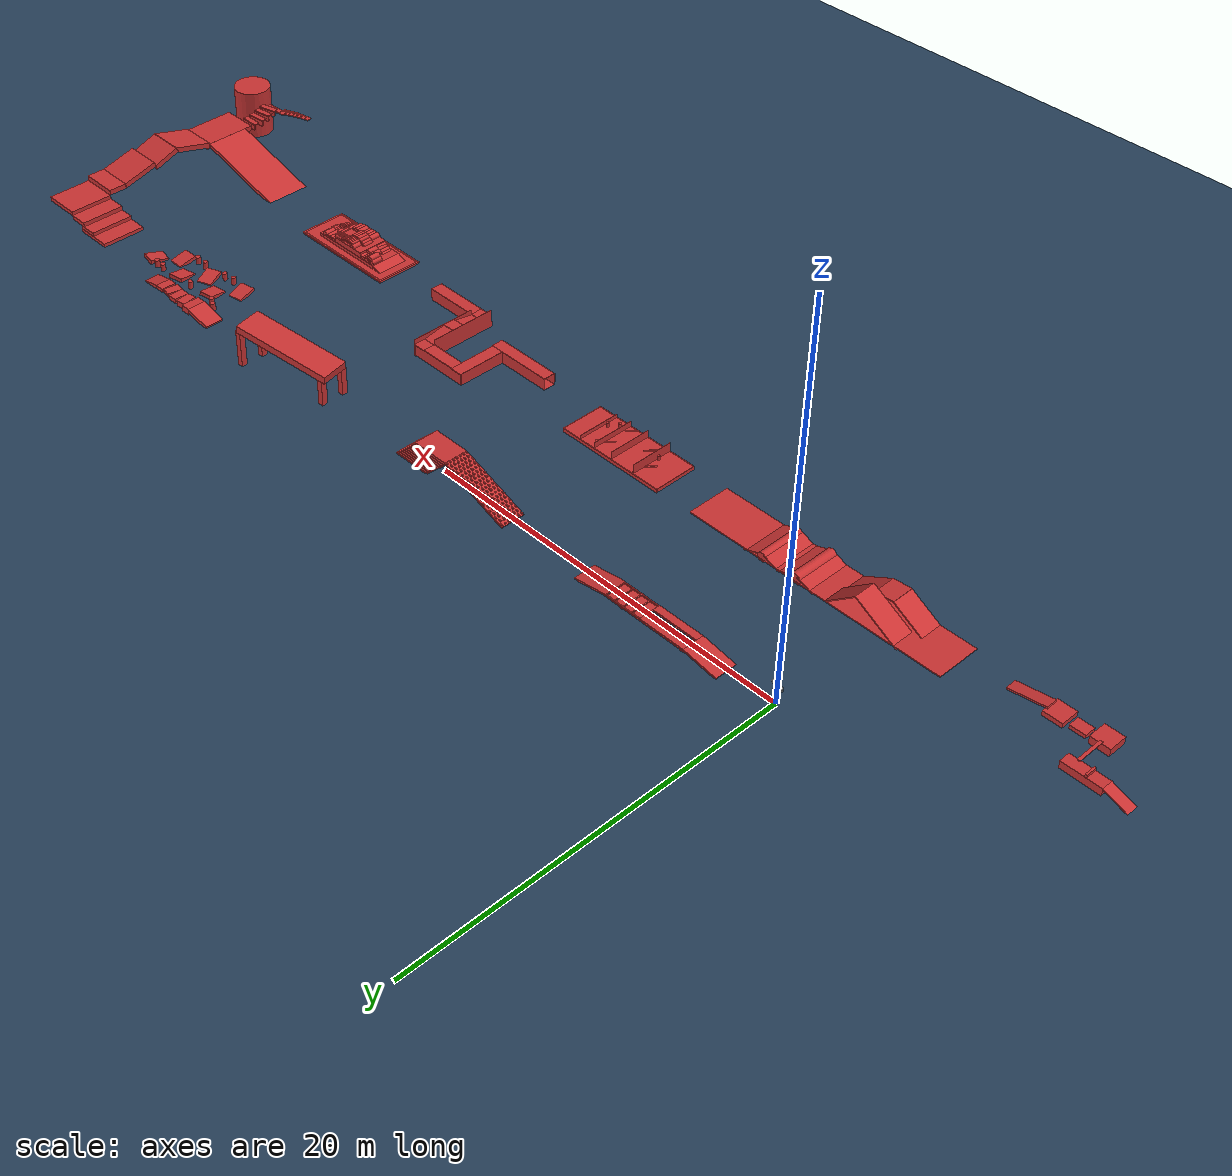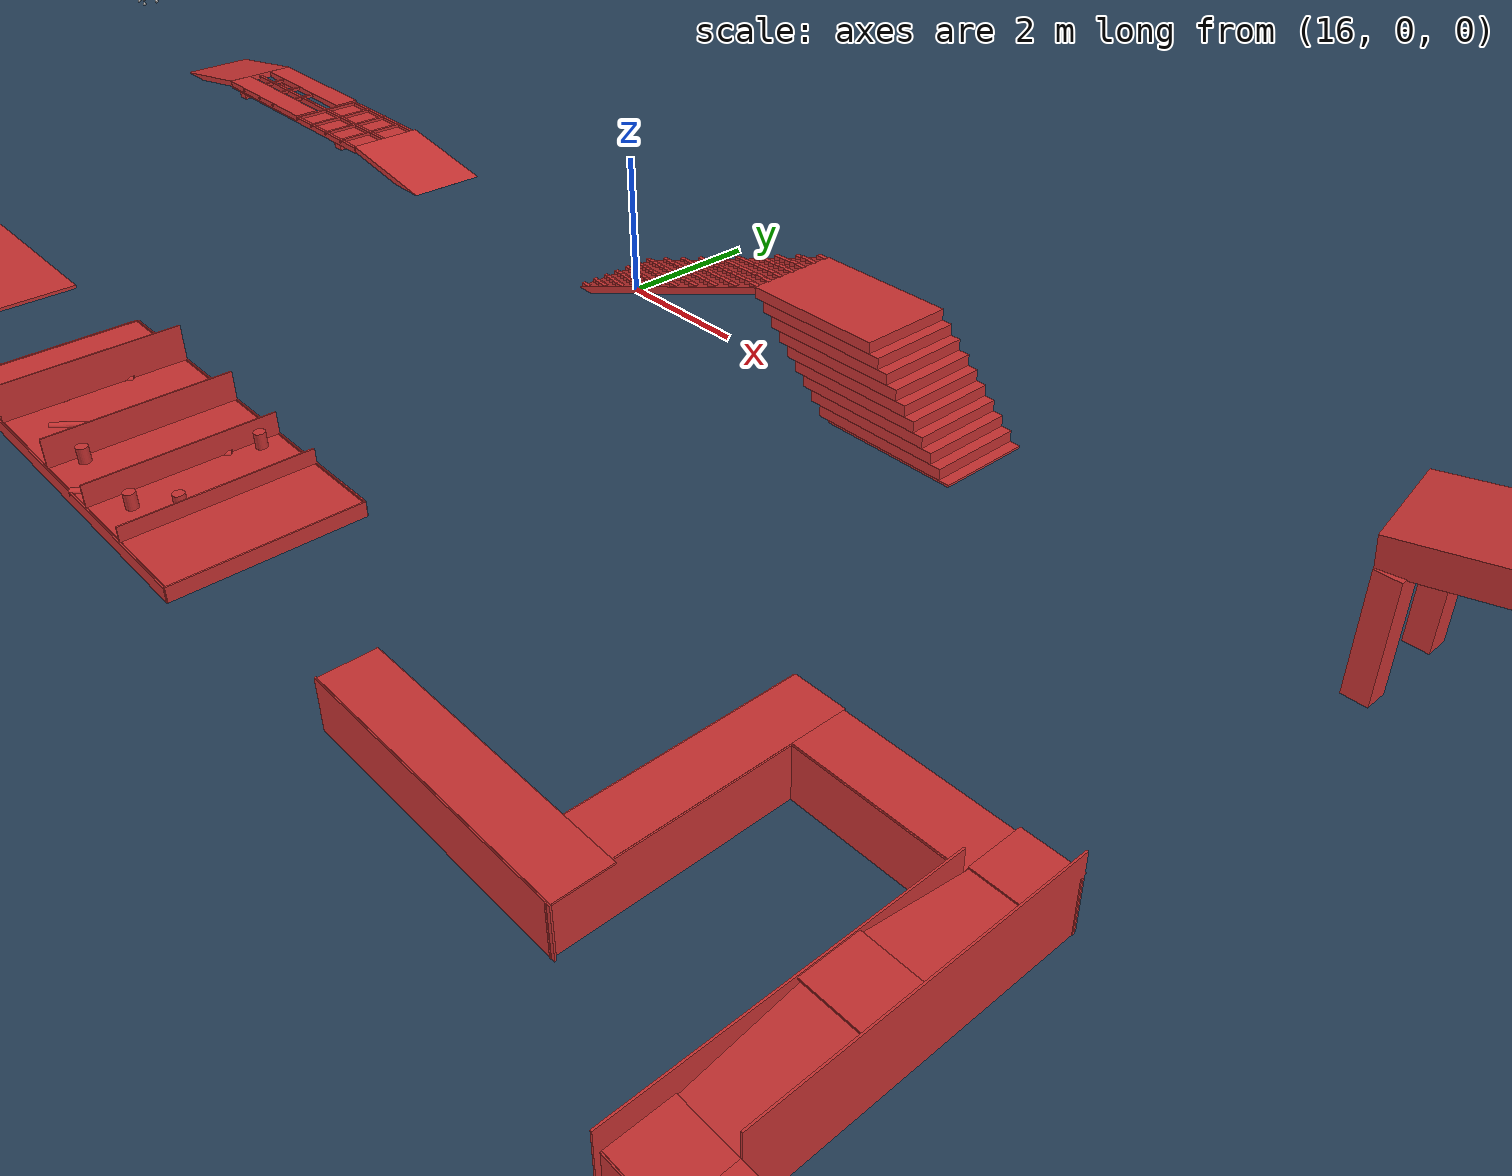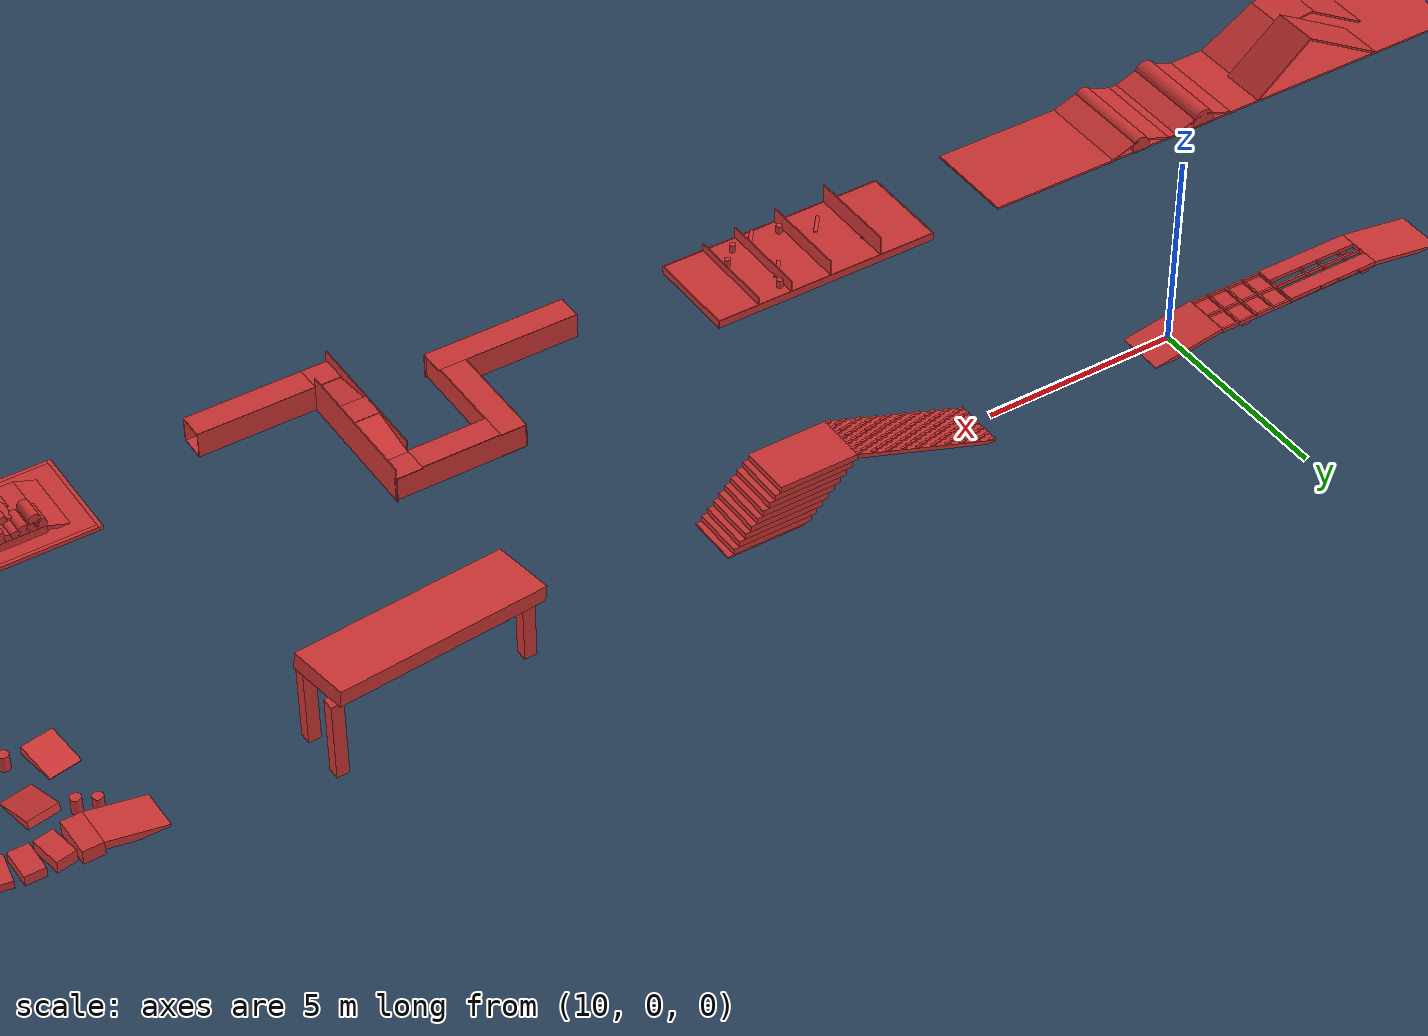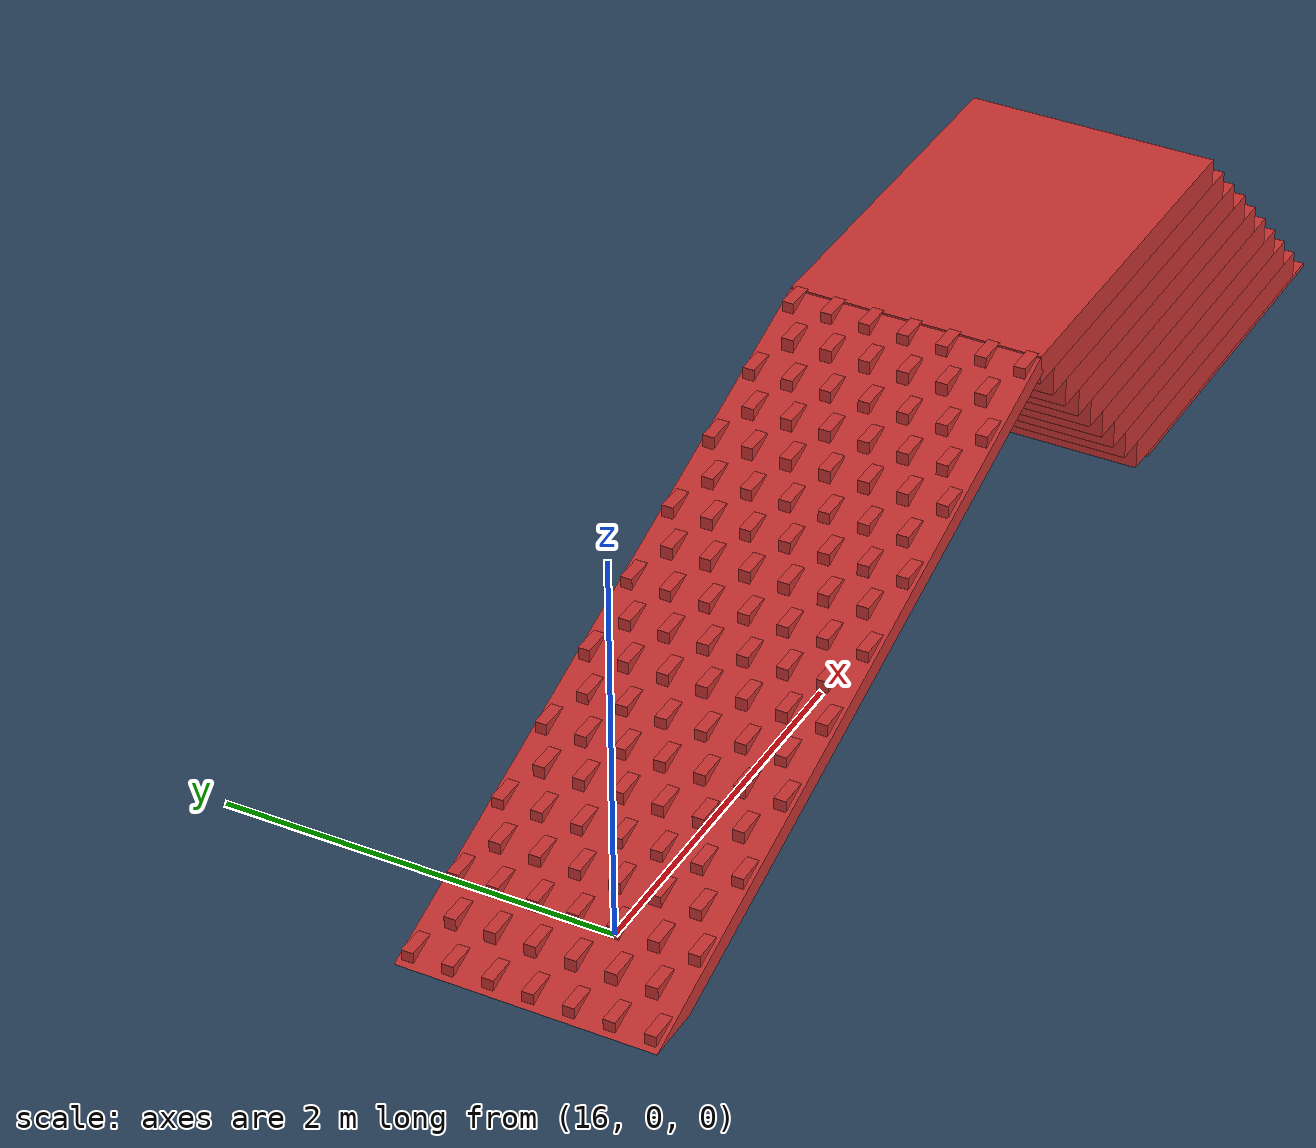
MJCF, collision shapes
<mujoco model="XXG scene">
  <include file="xxg.xml" />
  <statistic center="0 0 0.1" extent="0.8" />
  <visual>
    <headlight diffuse="0.6 0.6 0.6" ambient="0.3 0.3 0.3" specular="0 0 0" />
    <rgba haze="0.15 0.25 0.35 1" />
    <global azimuth="-130" elevation="-20" />
    <map znear="0.01" zfar="100"/>
  </visual>
  <asset>
    <texture type="skybox" builtin="gradient" rgb1="0.3 0.5 0.7" rgb2="0 0 0" width="512" height="3072" />
    <texture type="2d" name="groundplane" builtin="checker" mark="edge" rgb1="0.2 0.3 0.4" rgb2="0.1 0.2 0.3" markrgb="0.8 0.8 0.8" width="300" height="300" />
    <material name="groundplane" texture="groundplane" texuniform="true" texrepeat="5 5" reflectance="0.2" />
  <hfield name="perlin_hfield" size="1.0 0.75 0.2 0.2" file="../height_field.png" /><hfield name="image_hfield" size="1.0 1.0 0.02 0.1" file="../unitree_hfield.png" /></asset>
  <worldbody>
    <light pos="0 0 1.5" dir="0 0 -1" directional="true" />
    <geom name="floor" pos="0 0.0 0.01" size="0 0 0.01" type="plane" material="groundplane" />
<geom name="Phs_Cube2" type="box" size="1.25 0.2 0.05" pos="5.75 0.5 0.25" quat="1.0 0.0 0.0 0.0" rgba="0.8 0.2 0.2 1" solref="0.02 1" solimp="0.9 0.95 0.001"/>
<geom name="Phs_Cube3" type="box" size="0.95 0.6 0.05" pos="3.57 0.1 0.1" quat="0.996744 0.0 -0.080634 0.0" rgba="0.8 0.2 0.2 1" solref="0.02 1" solimp="0.9 0.95 0.001"/>
<geom name="Phs_Cube4" type="box" size="0.95 0.6 0.05" pos="9.94 0.1 0.1" quat="0.996744 0.0 0.080634 0.0" rgba="0.8 0.2 0.2 1" solref="0.02 1" solimp="0.9 0.95 0.001"/>
<geom name="Phs_Cube5" type="box" size="0.1 0.1 0.1" pos="4.7 -0.3 0.1" quat="1.0 0.0 0.0 0.0" rgba="0.8 0.2 0.2 1" solref="0.02 1" solimp="0.9 0.95 0.001"/>
<geom name="Phs_Cube6" type="box" size="0.1 0.1 0.1" pos="4.7 0.5 0.1" quat="1.0 0.0 0.0 0.0" rgba="0.8 0.2 0.2 1" solref="0.02 1" solimp="0.9 0.95 0.001"/>
<geom name="Phs_Cube7" type="box" size="0.1 0.1 0.1" pos="8.2 0.5 0.1" quat="1.0 0.0 0.0 0.0" rgba="0.8 0.2 0.2 1" solref="0.02 1" solimp="0.9 0.95 0.001"/>
<geom name="Phs_Cube8" type="box" size="0.1 0.1 0.1" pos="8.2 -0.3 0.1" quat="1.0 0.0 0.0 0.0" rgba="0.8 0.2 0.2 1" solref="0.02 1" solimp="0.9 0.95 0.001"/>
<geom name="Phs_Cube9" type="box" size="2.0 0.65 0.05" pos="17.27 0.1 0.64" quat="0.984808 0.0 -0.173648 0.0" rgba="0.8 0.2 0.2 1" solref="0.02 1" solimp="0.9 0.95 0.001"/>
<geom name="Phs_Cube10" type="box" size="1.0 0.65 0.075" pos="20.14 0.1 1.3" quat="1.0 0.0 0.0 0.0" rgba="0.8 0.2 0.2 1" solref="0.02 1" solimp="0.9 0.95 0.001"/>
<geom name="Phs_Cube11" type="box" size="1.0 0.65 0.075" pos="20.29 0.1 1.15" quat="1.0 0.0 0.0 0.0" rgba="0.8 0.2 0.2 1" solref="0.02 1" solimp="0.9 0.95 0.001"/>
<geom name="Phs_Cube12" type="box" size="1.0 0.65 0.075" pos="20.44 0.1 1.0" quat="1.0 0.0 0.0 0.0" rgba="0.8 0.2 0.2 1" solref="0.02 1" solimp="0.9 0.95 0.001"/>
<geom name="Phs_Cube13" type="box" size="1.0 0.65 0.075" pos="20.6 0.1 0.85" quat="1.0 0.0 0.0 0.0" rgba="0.8 0.2 0.2 1" solref="0.02 1" solimp="0.9 0.95 0.001"/>
<geom name="Phs_Cube14" type="box" size="1.0 0.65 0.075" pos="20.75 0.1 0.7" quat="1.0 0.0 0.0 0.0" rgba="0.8 0.2 0.2 1" solref="0.02 1" solimp="0.9 0.95 0.001"/>
<geom name="Phs_Cube15" type="box" size="1.0 0.65 0.075" pos="20.9 0.1 0.55" quat="1.0 0.0 0.0 0.0" rgba="0.8 0.2 0.2 1" solref="0.02 1" solimp="0.9 0.95 0.001"/>
<geom name="Phs_Cube16" type="box" size="1.0 0.65 0.075" pos="21.05 0.1 0.4" quat="1.0 0.0 0.0 0.0" rgba="0.8 0.2 0.2 1" solref="0.02 1" solimp="0.9 0.95 0.001"/>
<geom name="Phs_Cube17" type="box" size="1.0 0.65 0.075" pos="21.2 0.1 0.25" quat="1.0 0.0 0.0 0.0" rgba="0.8 0.2 0.2 1" solref="0.02 1" solimp="0.9 0.95 0.001"/>
<geom name="Phs_Cube18" type="box" size="1.0 0.65 0.075" pos="21.35 0.1 0.1" quat="1.0 0.0 0.0 0.0" rgba="0.8 0.2 0.2 1" solref="0.02 1" solimp="0.9 0.95 0.001"/>
<geom name="Phs_Cube19" type="box" size="1.0 0.65 0.075" pos="21.5 0.1 -0.05" quat="1.0 0.0 0.0 0.0" rgba="0.8 0.2 0.2 1" solref="0.02 1" solimp="0.9 0.95 0.001"/>
<geom name="Phs_Cube20" type="box" size="0.075 0.03 0.05" pos="15.48 0.7 0.02" quat="1.0 0.0 0.0 0.0" rgba="0.8 0.2 0.2 1" solref="0.02 1" solimp="0.9 0.95 0.001"/>
<geom name="Phs_Cube80" type="box" size="0.15 0.15 0.75" pos="27.64 -0.3 0.75" quat="1.0 0.0 0.0 0.0" rgba="0.8 0.2 0.2 1" solref="0.02 1" solimp="0.9 0.95 0.001"/>
<geom name="Phs_Cube81" type="box" size="0.15 0.15 0.75" pos="27.64 0.9 0.75" quat="1.0 0.0 0.0 0.0" rgba="0.8 0.2 0.2 1" solref="0.02 1" solimp="0.9 0.95 0.001"/>
<geom name="Phs_Cube82" type="box" size="0.15 0.15 1.0" pos="32.64 0.6 1.0" quat="1.0 0.0 0.0 0.0" rgba="0.8 0.2 0.2 1" solref="0.02 1" solimp="0.9 0.95 0.001"/>
<geom name="Phs_Cube83" type="box" size="0.15 0.15 1.0" pos="32.64 1.8 1.0" quat="1.0 0.0 0.0 0.0" rgba="0.8 0.2 0.2 1" solref="0.02 1" solimp="0.9 0.95 0.001"/>
<geom name="Phs_Cube84" type="box" size="2.75 0.75 0.2" pos="30.03 0.8 1.92" quat="0.994668 -0.010594 -0.053477 0.08754" rgba="0.8 0.2 0.2 1" solref="0.02 1" solimp="0.9 0.95 0.001"/>
<geom name="Phs_Cube85" type="box" size="0.75 0.5 0.1" pos="36.99 0.8 0.095" quat="0.994522 0.0 -0.104528 0.0" rgba="0.8 0.2 0.2 1" solref="0.02 1" solimp="0.9 0.95 0.001"/>
<geom name="Phs_Cube86" type="box" size="0.25 0.5 0.175" pos="37.95 0.8 0.175" quat="1.0 0.0 0.0 0.0" rgba="0.8 0.2 0.2 1" solref="0.02 1" solimp="0.9 0.95 0.001"/>
<geom name="Phs_Cube87" type="box" size="0.25 0.4 0.15" pos="38.56 0.8 0.15" quat="0.996195 0.0 0.0 0.087156" rgba="0.8 0.2 0.2 1" solref="0.02 1" solimp="0.9 0.95 0.001"/>
<geom name="Phs_Cube88" type="box" size="0.25 0.4 0.125" pos="39.19 0.8 0.125" quat="1.0 0.0 0.0 0.0" rgba="0.8 0.2 0.2 1" solref="0.02 1" solimp="0.9 0.95 0.001"/>
<geom name="Phs_Cube89" type="box" size="0.25 0.4 0.1" pos="39.81 0.7 0.1" quat="0.996195 0.0 0.0 -0.087156" rgba="0.8 0.2 0.2 1" solref="0.02 1" solimp="0.9 0.95 0.001"/>
<geom name="Phs_Cube90" type="box" size="0.5 0.4 0.1" pos="41.12 0.7 0.0" quat="0.994522 0.0 0.104528 0.0" rgba="0.8 0.2 0.2 1" solref="0.02 1" solimp="0.9 0.95 0.001"/>
<geom name="Phs_Cube91" type="box" size="0.25 0.4 0.1" pos="40.41 0.7 0.1" quat="1.0 0.0 0.0 0.0" rgba="0.8 0.2 0.2 1" solref="0.02 1" solimp="0.9 0.95 0.001"/>
<geom name="Phs_Cube92" type="box" size="0.5 0.4 0.1" pos="37.42 -1.77 0.02" quat="0.761848 -0.06719 -0.080073 -0.639266" rgba="0.8 0.2 0.2 1" solref="0.02 1" solimp="0.9 0.95 0.001"/>
<geom name="Phs_Cube93" type="box" size="0.5 0.4 0.1" pos="38.41 -0.7 0.02" quat="0.761848 0.06719 0.080073 -0.639266" rgba="0.8 0.2 0.2 1" solref="0.02 1" solimp="0.9 0.95 0.001"/>
<geom name="Phs_Cube98" type="box" size="1.0 1.2 0.1" pos="46.5 -0.3 0.1" quat="1.0 0.0 0.0 0.0" rgba="0.8 0.2 0.2 1" solref="0.02 1" solimp="0.9 0.95 0.001"/>
<geom name="Phs_Cube99" type="box" size="3.0 1.2 0.1" pos="45.43 -9.22 0.44" quat="0.991894 0.0 -0.127065 0.0" rgba="0.8 0.2 0.2 1" solref="0.02 1" solimp="0.9 0.95 0.001"/>
<geom name="Phs_Cube100" type="box" size="0.5 1.2 0.099" pos="47.0 -0.3 0.3" quat="1.0 0.0 0.0 0.0" rgba="0.8 0.2 0.2 1" solref="0.02 1" solimp="0.9 0.95 0.001"/>
<geom name="Phs_Cube101" type="box" size="0.5 1.2 0.117" pos="47.8 -0.3 0.515" quat="1.0 0.0 0.0 0.0" rgba="0.8 0.2 0.2 1" solref="0.02 1" solimp="0.9 0.95 0.001"/>
<geom name="Phs_Cube102" type="box" size="1.0 1.2 0.117" pos="49.3 -0.3 0.72" quat="1.0 0.0 0.0 0.0" rgba="0.8 0.2 0.2 1" solref="0.02 1" solimp="0.9 0.95 0.001"/>
<geom name="Phs_Cube103" type="box" size="1.0 0.5 0.143" pos="49.3 -1.99 0.98" quat="1.0 0.0 0.0 0.0" rgba="0.8 0.2 0.2 1" solref="0.02 1" solimp="0.9 0.95 0.001"/>
<geom name="Phs_Cube104" type="box" size="1.0 1.0 0.143" pos="49.3 -3.48 1.23" quat="0.991445 -0.130526 0.0 0.0" rgba="0.8 0.2 0.2 1" solref="0.02 1" solimp="0.9 0.95 0.001"/>
<geom name="Phs_Cube105" type="box" size="1.0 0.75 0.143" pos="49.3 -5.22 1.52" quat="0.984808 -0.173648 0.0 0.0" rgba="0.8 0.2 0.2 1" solref="0.02 1" solimp="0.9 0.95 0.001"/>
<geom name="Phs_Cube106" type="box" size="1.0 1.1 0.143" pos="49.3 -6.91 1.5" quat="0.991445 0.130526 0.0 0.0" rgba="0.8 0.2 0.2 1" solref="0.02 1" solimp="0.9 0.95 0.001"/>
<geom name="Phs_Cube108" type="box" size="1.0 1.5 0.143" pos="49.3 -9.33 1.15" quat="1.0 0.0 0.0 0.0" rgba="0.8 0.2 0.2 1" solref="0.02 1" solimp="0.9 0.95 0.001"/>
<geom name="Phs_Cube130_water" type="box" size="3.0 1.2 0.05" pos="36.5 -8.73 0.05" quat="1.0 0.0 0.0 0.0" rgba="0.8 0.2 0.2 1" solref="0.02 1" solimp="0.9 0.95 0.001"/>
<geom name="Phs_Cube131" type="box" size="1.0 0.85 0.15" pos="36.5 -8.73 0.45" quat="1.0 0.0 0.0 0.0" rgba="0.8 0.2 0.2 1" solref="0.02 1" solimp="0.9 0.95 0.001"/>
<geom name="Phs_Cylinder_Rock81"  type="cylinder" size="0.15 0.3" pos="38.65 -8.2 0.14" quat="0.707107 -0.707107 0.0 0.0" rgba="0.8 0.2 0.2 1" solref="0.002 1" solimp="0.95 0.99 0.0005" condim="4"/>
<geom name="Phs_Cube132" type="box" size="2.0 0.85 0.15" pos="36.5 -8.73 0.15" quat="1.0 0.0 0.0 0.0" rgba="0.8 0.2 0.2 1" solref="0.02 1" solimp="0.9 0.95 0.001"/>
<geom name="Phs_Cube133" type="box" size="0.05 1.3 0.05" pos="39.55 -8.73 0.05" quat="1.0 0.0 0.0 0.0" rgba="0.8 0.2 0.2 1" solref="0.02 1" solimp="0.9 0.95 0.001"/>
<geom name="Phs_Cube134" type="box" size="3.0 0.05 0.05" pos="36.5 -9.98 0.05" quat="1.0 0.0 0.0 0.0" rgba="0.8 0.2 0.2 1" solref="0.02 1" solimp="0.9 0.95 0.001"/>
<geom name="Phs_Cube135" type="box" size="0.05 1.3 0.05" pos="33.45 -8.73 0.05" quat="1.0 0.0 0.0 0.0" rgba="0.8 0.2 0.2 1" solref="0.02 1" solimp="0.9 0.95 0.001"/>
<geom name="Phs_Cube136" type="box" size="3.0 0.05 0.05" pos="36.5 -7.48 0.05" quat="1.0 0.0 0.0 0.0" rgba="0.8 0.2 0.2 1" solref="0.02 1" solimp="0.9 0.95 0.001"/>
<geom name="Phs_Cylinder_Rock80"  type="cylinder" size="0.075 0.15" pos="38.58 -9.4 0.15" quat="0.707107 -0.707107 0.0 0.0" rgba="0.8 0.2 0.2 1" solref="0.002 1" solimp="0.95 0.99 0.0005" condim="4"/>
<geom name="Phs_Cylinder_Rock79"  type="cylinder" size="0.075 0.15" pos="38.69 -9.4 0.05" quat="0.707107 -0.707107 0.0 0.0" rgba="0.8 0.2 0.2 1" solref="0.002 1" solimp="0.95 0.99 0.0005" condim="4"/>
<geom name="Phs_Cylinder_Rock78"  type="cylinder" size="0.1 0.2" pos="38.65 -8.7 0.1" quat="0.707107 -0.707107 0.0 0.0" rgba="0.8 0.2 0.2 1" solref="0.002 1" solimp="0.95 0.99 0.0005" condim="4"/>
<geom name="Phs_Cylinder_Rock77"  type="cylinder" size="0.075 0.15" pos="38.69 -8.8 0.25" quat="0.707107 -0.707107 0.0 0.0" rgba="0.8 0.2 0.2 1" solref="0.002 1" solimp="0.95 0.99 0.0005" condim="4"/>
<geom name="Phs_Cylinder_Rock76"  type="cylinder" size="0.1 0.175" pos="38.6 -9.07 0.1" quat="0.707107 -0.707107 0.0 0.0" rgba="0.8 0.2 0.2 1" solref="0.002 1" solimp="0.95 0.99 0.0005" condim="4"/>
<geom name="Phs_Cylinder_Rock75"  type="cylinder" size="0.1 0.175" pos="38.7 -9.07 0.1" quat="0.707107 -0.707107 0.0 0.0" rgba="0.8 0.2 0.2 1" solref="0.002 1" solimp="0.95 0.99 0.0005" condim="4"/>
<geom name="Phs_Cylinder_Rock74"  type="cylinder" size="0.075 0.15" pos="38.69 -8.8 0.25" quat="0.707107 -0.707107 0.0 0.0" rgba="0.8 0.2 0.2 1" solref="0.002 1" solimp="0.95 0.99 0.0005" condim="4"/>
<geom name="Phs_Cylinder_Rock73"  type="cylinder" size="0.1 0.3" pos="38.05 -8.75 0.35" quat="0.707107 -0.707107 0.0 0.0" rgba="0.8 0.2 0.2 1" solref="0.002 1" solimp="0.95 0.99 0.0005" condim="4"/>
<geom name="Phs_Cylinder_Rock72"  type="cylinder" size="0.125 0.3" pos="37.65 -8.2 0.34" quat="0.707107 -0.707107 0.0 0.0" rgba="0.8 0.2 0.2 1" solref="0.002 1" solimp="0.95 0.99 0.0005" condim="4"/>
<geom name="Phs_Cylinder_Rock71"  type="cylinder" size="0.075 0.25" pos="37.59 -8.75 0.35" quat="0.707107 -0.707107 0.0 0.0" rgba="0.8 0.2 0.2 1" solref="0.002 1" solimp="0.95 0.99 0.0005" condim="4"/>
<geom name="Phs_Cylinder_Rock70"  type="cylinder" size="0.15 0.3" pos="38.35 -8.2 0.34" quat="0.707107 -0.707107 0.0 0.0" rgba="0.8 0.2 0.2 1" solref="0.002 1" solimp="0.95 0.99 0.0005" condim="4"/>
<geom name="Phs_Cylinder_Rock69"  type="cylinder" size="0.125 0.3" pos="37.85 -8.2 0.34" quat="0.707107 -0.707107 0.0 0.0" rgba="0.8 0.2 0.2 1" solref="0.002 1" solimp="0.95 0.99 0.0005" condim="4"/>
<geom name="Phs_Cylinder_Rock68"  type="cylinder" size="0.125 0.3" pos="38.09 -8.2 0.34" quat="0.707107 -0.707107 0.0 0.0" rgba="0.8 0.2 0.2 1" solref="0.002 1" solimp="0.95 0.99 0.0005" condim="4"/>
<geom name="Phs_Cylinder_Rock67"  type="cylinder" size="0.075 0.15" pos="38.59 -9.1 0.25" quat="0.707107 -0.707107 0.0 0.0" rgba="0.8 0.2 0.2 1" solref="0.002 1" solimp="0.95 0.99 0.0005" condim="4"/>
<geom name="Phs_Cylinder_Rock66"  type="cylinder" size="0.075 0.3" pos="38.49 -8.7 0.34" quat="0.707107 -0.707107 0.0 0.0" rgba="0.8 0.2 0.2 1" solref="0.002 1" solimp="0.95 0.99 0.0005" condim="4"/>
<geom name="Phs_Cylinder_Rock65"  type="cylinder" size="0.1 0.3" pos="38.29 -8.7 0.34" quat="0.707107 -0.707107 0.0 0.0" rgba="0.8 0.2 0.2 1" solref="0.002 1" solimp="0.95 0.99 0.0005" condim="4"/>
<geom name="Phs_Cylinder_Rock64"  type="cylinder" size="0.15 0.3" pos="37.65 -9.3 0.34" quat="0.707107 -0.707107 0.0 0.0" rgba="0.8 0.2 0.2 1" solref="0.002 1" solimp="0.95 0.99 0.0005" condim="4"/>
<geom name="Phs_Cylinder_Rock62"  type="cylinder" size="0.075 0.15" pos="38.25 -9.4 0.35" quat="0.707107 -0.707107 0.0 0.0" rgba="0.8 0.2 0.2 1" solref="0.002 1" solimp="0.95 0.99 0.0005" condim="4"/>
<geom name="Phs_Cylinder_Rock61"  type="cylinder" size="0.075 0.15" pos="38.13 -9.4 0.35" quat="0.707107 -0.707107 0.0 0.0" rgba="0.8 0.2 0.2 1" solref="0.002 1" solimp="0.95 0.99 0.0005" condim="4"/>
<geom name="Phs_Cylinder_Rock60"  type="cylinder" size="0.075 0.15" pos="38.02 -9.4 0.35" quat="0.707107 -0.707107 0.0 0.0" rgba="0.8 0.2 0.2 1" solref="0.002 1" solimp="0.95 0.99 0.0005" condim="4"/>
<geom name="Phs_Cylinder_Rock59"  type="cylinder" size="0.1 0.3" pos="37.89 -9.3 0.34" quat="0.707107 -0.707107 0.0 0.0" rgba="0.8 0.2 0.2 1" solref="0.002 1" solimp="0.95 0.99 0.0005" condim="4"/>
<geom name="Phs_Cylinder_Rock58"  type="cylinder" size="0.1 0.3" pos="38.15 -9.11 0.34" quat="0.5 -0.5 0.5 -0.5" rgba="0.8 0.2 0.2 1" solref="0.002 1" solimp="0.95 0.99 0.0005" condim="4"/>
<geom name="Phs_Cylinder_Rock63"  type="cylinder" size="0.15 0.35" pos="37.85 -8.7 0.27" quat="0.707107 -0.707107 0.0 0.0" rgba="0.8 0.2 0.2 1" solref="0.002 1" solimp="0.95 0.99 0.0005" condim="4"/>
<geom name="Phs_Cylinder_Rock57"  type="cylinder" size="0.075 0.15" pos="38.15 -9.2 0.42" quat="0.5 -0.5 -0.5 0.5" rgba="0.8 0.2 0.2 1" solref="0.002 1" solimp="0.95 0.99 0.0005" condim="4"/>
<geom name="Phs_Cylinder_Rock56"  type="cylinder" size="0.075 0.3" pos="38.21 -8.8 0.35" quat="0.707107 -0.707107 0.0 0.0" rgba="0.8 0.2 0.2 1" solref="0.002 1" solimp="0.95 0.99 0.0005" condim="4"/>
<geom name="Phs_Cylinder_Rock55"  type="cylinder" size="0.075 0.25" pos="37.69 -8.75 0.35" quat="0.707107 -0.707107 0.0 0.0" rgba="0.8 0.2 0.2 1" solref="0.002 1" solimp="0.95 0.99 0.0005" condim="4"/>
<geom name="Phs_Cylinder_Rock54"  type="cylinder" size="0.125 0.3" pos="37.65 -8.2 0.34" quat="0.707107 -0.707107 0.0 0.0" rgba="0.8 0.2 0.2 1" solref="0.002 1" solimp="0.95 0.99 0.0005" condim="4"/>
<geom name="Phs_Cylinder_Rock53"  type="cylinder" size="0.075 0.15" pos="38.15 -9.0 0.42" quat="0.5 -0.5 -0.5 0.5" rgba="0.8 0.2 0.2 1" solref="0.002 1" solimp="0.95 0.99 0.0005" condim="4"/>
<geom name="Phs_Cylinder_Rock52"  type="cylinder" size="0.075 0.15" pos="38.15 -8.9 0.42" quat="0.5 -0.5 -0.5 0.5" rgba="0.8 0.2 0.2 1" solref="0.002 1" solimp="0.95 0.99 0.0005" condim="4"/>
<geom name="Phs_Cylinder_Rock51"  type="cylinder" size="0.075 0.25" pos="37.79 -8.75 0.45" quat="0.707107 -0.707107 0.0 0.0" rgba="0.8 0.2 0.2 1" solref="0.002 1" solimp="0.95 0.99 0.0005" condim="4"/>
<geom name="Phs_Cylinder_Rock50"  type="cylinder" size="0.075 0.25" pos="37.65 -8.75 0.45" quat="0.707107 -0.707107 0.0 0.0" rgba="0.8 0.2 0.2 1" solref="0.002 1" solimp="0.95 0.99 0.0005" condim="4"/>
<geom name="Phs_Cylinder_Rock49"  type="cylinder" size="0.075 0.25" pos="37.55 -8.75 0.45" quat="0.707107 -0.707107 0.0 0.0" rgba="0.8 0.2 0.2 1" solref="0.002 1" solimp="0.95 0.99 0.0005" condim="4"/>
<geom name="Phs_Cylinder_Rock48"  type="cylinder" size="0.15 0.3" pos="36.85 -8.7 0.54" quat="0.707107 -0.707107 0.0 0.0" rgba="0.8 0.2 0.2 1" solref="0.002 1" solimp="0.95 0.99 0.0005" condim="4"/>
<geom name="Phs_Cylinder_Rock47"  type="cylinder" size="0.1 0.3" pos="37.39 -9.3 0.64" quat="0.707107 -0.707107 0.0 0.0" rgba="0.8 0.2 0.2 1" solref="0.002 1" solimp="0.95 0.99 0.0005" condim="4"/>
<geom name="Phs_Cylinder_Rock46"  type="cylinder" size="0.15 0.3" pos="37.15 -9.3 0.64" quat="0.707107 -0.707107 0.0 0.0" rgba="0.8 0.2 0.2 1" solref="0.002 1" solimp="0.95 0.99 0.0005" condim="4"/>
<geom name="Phs_Cylinder_Rock45"  type="cylinder" size="0.15 0.3" pos="36.95 -9.3 0.64" quat="0.707107 -0.707107 0.0 0.0" rgba="0.8 0.2 0.2 1" solref="0.002 1" solimp="0.95 0.99 0.0005" condim="4"/>
<geom name="Phs_Cylinder_Rock44"  type="cylinder" size="0.1 0.3" pos="36.72 -9.3 0.64" quat="0.707107 -0.707107 0.0 0.0" rgba="0.8 0.2 0.2 1" solref="0.002 1" solimp="0.95 0.99 0.0005" condim="4"/>
<geom name="Phs_Cylinder_Rock43"  type="cylinder" size="0.15 0.3" pos="36.65 -8.69 0.64" quat="0.707107 -0.707107 0.0 0.0" rgba="0.8 0.2 0.2 1" solref="0.002 1" solimp="0.95 0.99 0.0005" condim="4"/>
<geom name="Phs_Cylinder_Rock42"  type="cylinder" size="0.15 0.3" pos="36.49 -9.29 0.64" quat="0.707107 -0.707107 0.0 0.0" rgba="0.8 0.2 0.2 1" solref="0.002 1" solimp="0.95 0.99 0.0005" condim="4"/>
<geom name="Phs_Cylinder_Rock41"  type="cylinder" size="0.075 0.25" pos="37.25 -8.35 0.6" quat="0.5 0.5 0.5 0.5" rgba="0.8 0.2 0.2 1" solref="0.002 1" solimp="0.95 0.99 0.0005" condim="4"/>
<geom name="Phs_Cylinder_Rock40"  type="cylinder" size="0.075 0.25" pos="37.25 -8.25 0.63" quat="0.5 0.5 0.5 0.5" rgba="0.8 0.2 0.2 1" solref="0.002 1" solimp="0.95 0.99 0.0005" condim="4"/>
<geom name="Phs_Cylinder_Rock39"  type="cylinder" size="0.075 0.25" pos="37.25 -8.15 0.67" quat="0.5 0.5 0.5 0.5" rgba="0.8 0.2 0.2 1" solref="0.002 1" solimp="0.95 0.99 0.0005" condim="4"/>
<geom name="Phs_Cylinder_Rock38"  type="cylinder" size="0.075 0.25" pos="37.25 -8.05 0.67" quat="0.5 0.5 0.5 0.5" rgba="0.8 0.2 0.2 1" solref="0.002 1" solimp="0.95 0.99 0.0005" condim="4"/>
<geom name="Phs_Cylinder_Rock37"  type="cylinder" size="0.075 0.25" pos="37.25 -7.95 0.67" quat="0.5 0.5 0.5 0.5" rgba="0.8 0.2 0.2 1" solref="0.002 1" solimp="0.95 0.99 0.0005" condim="4"/>
<geom name="Phs_Cylinder_Rock36"  type="cylinder" size="0.15 0.3" pos="36.45 -8.69 0.71" quat="0.707107 -0.707107 0.0 0.0" rgba="0.8 0.2 0.2 1" solref="0.002 1" solimp="0.95 0.99 0.0005" condim="4"/>
<geom name="Phs_Cylinder_Rock35"  type="cylinder" size="0.1 0.3" pos="36.72 -8.69 0.74" quat="0.707107 -0.707107 0.0 0.0" rgba="0.8 0.2 0.2 1" solref="0.002 1" solimp="0.95 0.99 0.0005" condim="4"/>
<geom name="Phs_Cylinder_Rock34"  type="cylinder" size="0.1 0.3" pos="36.62 -8.69 0.84" quat="0.707107 -0.707107 0.0 0.0" rgba="0.8 0.2 0.2 1" solref="0.002 1" solimp="0.95 0.99 0.0005" condim="4"/>
<geom name="Phs_Cylinder_Rock33"  type="cylinder" size="0.1 0.3" pos="36.47 -8.69 0.84" quat="0.707107 -0.707107 0.0 0.0" rgba="0.8 0.2 0.2 1" solref="0.002 1" solimp="0.95 0.99 0.0005" condim="4"/>
<geom name="Phs_Cylinder_Rock32"  type="cylinder" size="0.075 0.25" pos="36.95 -8.15 0.67" quat="0.0 0.0 0.707107 0.707107" rgba="0.8 0.2 0.2 1" solref="0.002 1" solimp="0.95 0.99 0.0005" condim="4"/>
<geom name="Phs_Cylinder_Rock31"  type="cylinder" size="0.075 0.25" pos="36.83 -8.15 0.71" quat="0.0 0.0 0.707107 0.707107" rgba="0.8 0.2 0.2 1" solref="0.002 1" solimp="0.95 0.99 0.0005" condim="4"/>
<geom name="Phs_Cylinder_Rock30"  type="cylinder" size="0.075 0.25" pos="36.71 -8.15 0.75" quat="0.0 0.0 0.707107 0.707107" rgba="0.8 0.2 0.2 1" solref="0.002 1" solimp="0.95 0.99 0.0005" condim="4"/>
<geom name="Phs_Cylinder_Rock29"  type="cylinder" size="0.075 0.25" pos="36.61 -8.15 0.79" quat="0.0 0.0 0.707107 0.707107" rgba="0.8 0.2 0.2 1" solref="0.002 1" solimp="0.95 0.99 0.0005" condim="4"/>
<geom name="Phs_Cylinder_Rock28"  type="cylinder" size="0.075 0.25" pos="36.51 -8.15 0.79" quat="0.0 0.0 0.707107 0.707107" rgba="0.8 0.2 0.2 1" solref="0.002 1" solimp="0.95 0.99 0.0005" condim="4"/>
<geom name="Phs_Cylinder_Rock27"  type="cylinder" size="0.075 0.25" pos="36.41 -8.15 0.79" quat="0.0 0.0 0.707107 0.707107" rgba="0.8 0.2 0.2 1" solref="0.002 1" solimp="0.95 0.99 0.0005" condim="4"/>
<geom name="Phs_Cylinder_Rock26"  type="cylinder" size="0.075 0.25" pos="36.31 -8.15 0.79" quat="0.0 0.0 0.707107 0.707107" rgba="0.8 0.2 0.2 1" solref="0.002 1" solimp="0.95 0.99 0.0005" condim="4"/>
<geom name="Phs_Cylinder_Rock25"  type="cylinder" size="0.075 0.25" pos="36.21 -8.15 0.79" quat="0.0 0.0 0.707107 0.707107" rgba="0.8 0.2 0.2 1" solref="0.002 1" solimp="0.95 0.99 0.0005" condim="4"/>
<geom name="Phs_Cylinder_Rock24"  type="cylinder" size="0.1 0.3" pos="36.31 -8.69 0.84" quat="0.707107 -0.707107 0.0 0.0" rgba="0.8 0.2 0.2 1" solref="0.002 1" solimp="0.95 0.99 0.0005" condim="4"/>
<geom name="Phs_Cylinder_Rock23"  type="cylinder" size="0.1 0.3" pos="36.16 -8.69 0.78" quat="0.707107 -0.707107 0.0 0.0" rgba="0.8 0.2 0.2 1" solref="0.002 1" solimp="0.95 0.99 0.0005" condim="4"/>
<geom name="Phs_Cylinder_Rock22"  type="cylinder" size="0.15 0.3" pos="36.25 -8.69 0.71" quat="0.707107 -0.707107 0.0 0.0" rgba="0.8 0.2 0.2 1" solref="0.002 1" solimp="0.95 0.99 0.0005" condim="4"/>
<geom name="Phs_Cylinder_Rock21"  type="cylinder" size="0.15 0.3" pos="36.29 -9.29 0.64" quat="0.707107 -0.707107 0.0 0.0" rgba="0.8 0.2 0.2 1" solref="0.002 1" solimp="0.95 0.99 0.0005" condim="4"/>
<geom name="Phs_Cylinder_Rock20"  type="cylinder" size="0.15 0.3" pos="36.09 -9.29 0.64" quat="0.707107 -0.707107 0.0 0.0" rgba="0.8 0.2 0.2 1" solref="0.002 1" solimp="0.95 0.99 0.0005" condim="4"/>
<geom name="Phs_Cylinder_Rock19"  type="cylinder" size="0.1 0.3" pos="36.0 -8.69 0.68" quat="0.707107 -0.707107 0.0 0.0" rgba="0.8 0.2 0.2 1" solref="0.002 1" solimp="0.95 0.99 0.0005" condim="4"/>
<geom name="Phs_Cylinder_Rock18"  type="cylinder" size="0.1 0.3" pos="35.43 -9.19 0.48" quat="0.707107 -0.707107 0.0 0.0" rgba="0.8 0.2 0.2 1" solref="0.002 1" solimp="0.95 0.99 0.0005" condim="4"/>
<geom name="Phs_Cylinder_Rock17"  type="cylinder" size="0.15 0.3" pos="36.14 -8.19 0.6" quat="0.707107 -0.707107 0.0 0.0" rgba="0.8 0.2 0.2 1" solref="0.002 1" solimp="0.95 0.99 0.0005" condim="4"/>
<geom name="Phs_Cylinder_Rock16"  type="cylinder" size="0.1 0.3" pos="35.88 -8.69 0.61" quat="0.707107 -0.707107 0.0 0.0" rgba="0.8 0.2 0.2 1" solref="0.002 1" solimp="0.95 0.99 0.0005" condim="4"/>
<geom name="Phs_Cylinder_Rock15"  type="cylinder" size="0.1 0.3" pos="35.31 -9.19 0.42" quat="0.707107 -0.707107 0.0 0.0" rgba="0.8 0.2 0.2 1" solref="0.002 1" solimp="0.95 0.99 0.0005" condim="4"/>
<geom name="Phs_Cylinder_Rock14"  type="cylinder" size="0.1 0.3" pos="35.16 -9.19 0.33" quat="0.707107 -0.707107 0.0 0.0" rgba="0.8 0.2 0.2 1" solref="0.002 1" solimp="0.95 0.99 0.0005" condim="4"/>
<geom name="Phs_Cylinder_Rock13"  type="cylinder" size="0.1 0.3" pos="35.02 -9.19 0.25" quat="0.707107 -0.707107 0.0 0.0" rgba="0.8 0.2 0.2 1" solref="0.002 1" solimp="0.95 0.99 0.0005" condim="4"/>
<geom name="Phs_Cylinder_Rock8"  type="cylinder" size="0.1 0.3" pos="34.0 -8.69 -0.01" quat="0.707107 -0.707107 0.0 0.0" rgba="0.8 0.2 0.2 1" solref="0.002 1" solimp="0.95 0.99 0.0005" condim="4"/>
<geom name="Phs_Cylinder_Rock7"  type="cylinder" size="0.15 0.3" pos="35.37 -8.59 0.49" quat="0.707107 -0.707107 0.0 0.0" rgba="0.8 0.2 0.2 1" solref="0.002 1" solimp="0.95 0.99 0.0005" condim="4"/>
<geom name="Phs_Cylinder_Rock6"  type="cylinder" size="0.15 0.3" pos="35.47 -8.19 0.33" quat="0.707107 -0.707107 0.0 0.0" rgba="0.8 0.2 0.2 1" solref="0.002 1" solimp="0.95 0.99 0.0005" condim="4"/>
<geom name="Phs_Cylinder_Rock5"  type="cylinder" size="0.15 0.3" pos="35.23 -8.19 0.33" quat="0.707107 -0.707107 0.0 0.0" rgba="0.8 0.2 0.2 1" solref="0.002 1" solimp="0.95 0.99 0.0005" condim="4"/>
<geom name="Phs_Cylinder_Rock4"  type="cylinder" size="0.15 0.3" pos="35.17 -8.59 0.38" quat="0.707107 -0.707107 0.0 0.0" rgba="0.8 0.2 0.2 1" solref="0.002 1" solimp="0.95 0.99 0.0005" condim="4"/>
<geom name="Phs_Cylinder_Rock3"  type="cylinder" size="0.15 0.3" pos="35.03 -8.19 0.4" quat="0.707107 -0.707107 0.0 0.0" rgba="0.8 0.2 0.2 1" solref="0.002 1" solimp="0.95 0.99 0.0005" condim="4"/>
<geom name="Phs_Cylinder_Rock2"  type="cylinder" size="0.15 0.3" pos="34.83 -8.19 0.4" quat="0.707107 -0.707107 0.0 0.0" rgba="0.8 0.2 0.2 1" solref="0.002 1" solimp="0.95 0.99 0.0005" condim="4"/>
<geom name="Phs_Cylinder_Rock1"  type="cylinder" size="0.15 0.3" pos="34.63 -8.19 0.4" quat="0.707107 -0.707107 0.0 0.0" rgba="0.8 0.2 0.2 1" solref="0.002 1" solimp="0.95 0.99 0.0005" condim="4"/>
<geom name="Phs_Cylinder_Rock0"  type="cylinder" size="0.15 0.3" pos="34.76 -8.19 0.58" quat="0.707107 -0.707107 0.0 0.0" rgba="0.8 0.2 0.2 1" solref="0.002 1" solimp="0.95 0.99 0.0005" condim="4"/>
<geom name="Phs_Cube137" type="box" size="1.5 0.325 0.01" pos="29.05 -8.73 0.01" quat="1.0 0.0 0.0 0.0" rgba="0.8 0.2 0.2 1" solref="0.02 1" solimp="0.9 0.95 0.001"/>
<geom name="Phs_Cube138" type="box" size="1.5 0.325 0.01" pos="29.05 -8.41 0.33" quat="0.707107 -0.707107 0.0 0.0" rgba="0.8 0.2 0.2 1" solref="0.02 1" solimp="0.9 0.95 0.001"/>
<geom name="Phs_Cube139" type="box" size="1.825 0.325 0.01" pos="28.73 -9.06 0.33" quat="0.707107 -0.707107 0.0 0.0" rgba="0.8 0.2 0.2 1" solref="0.02 1" solimp="0.9 0.95 0.001"/>
<geom name="Phs_Cube140" type="box" size="1.5 0.325 0.01" pos="29.05 -8.73 0.65" quat="1.0 0.0 0.0 0.0" rgba="0.8 0.2 0.2 1" solref="0.02 1" solimp="0.9 0.95 0.001"/>
<geom name="Phs_Cube141" type="box" size="0.75 0.325 0.01" pos="27.25 -7.735719 0.746875" quat="0.704416 0.061628 0.061628 -0.704416" rgba="0.8 0.2 0.2 1" solref="0.02 1" solimp="0.9 0.95 0.001"/>
<geom name="Phs_Cube144" type="box" size="0.75 0.325 0.01" pos="27.25 -7.644281 0.12" quat="0.704416 0.061628 0.061628 -0.704416" rgba="0.8 0.2 0.2 1" solref="0.02 1" solimp="0.9 0.95 0.001"/>
<geom name="Phs_Cube145" type="box" size="0.75 0.325 0.01" pos="27.25 -6.18 0.12" quat="0.704416 -0.061628 -0.061628 -0.704416" rgba="0.8 0.2 0.2 1" solref="0.02 1" solimp="0.9 0.95 0.001"/>
<geom name="Phs_Cube148" type="box" size="0.75 0.325 0.01" pos="27.25 -6.07 0.77" quat="0.704416 -0.061628 -0.061628 -0.704416" rgba="0.8 0.2 0.2 1" solref="0.02 1" solimp="0.9 0.95 0.001"/>
<geom name="Phs_Cube149" type="box" size="1.0 0.325 0.01" pos="25.92 -5.41 0.33" quat="0.707107 -0.707107 0.0 0.0" rgba="0.8 0.2 0.2 1" solref="0.02 1" solimp="0.9 0.95 0.001"/>
<geom name="Phs_Cube150" type="box" size="1.0 0.325 0.01" pos="25.92 -5.09 0.01" quat="1.0 0.0 0.0 0.0" rgba="0.8 0.2 0.2 1" solref="0.02 1" solimp="0.9 0.95 0.001"/>
<geom name="Phs_Cube151" type="box" size="1.67 0.325 0.01" pos="25.93 -4.77 0.33" quat="0.707107 -0.707107 0.0 0.0" rgba="0.8 0.2 0.2 1" solref="0.02 1" solimp="0.9 0.95 0.001"/>
<geom name="Phs_Cube152" type="box" size="1.0 0.325 0.01" pos="25.92 -5.08 0.65" quat="1.0 0.0 0.0 0.0" rgba="0.8 0.2 0.2 1" solref="0.02 1" solimp="0.9 0.95 0.001"/>
<geom name="Phs_Cube153" type="box" size="1.335 0.325 0.01" pos="24.93 -6.74 0.33" quat="0.5 -0.5 -0.5 0.5" rgba="0.8 0.2 0.2 1" solref="0.02 1" solimp="0.9 0.95 0.001"/>
<geom name="Phs_Cube154" type="box" size="1.65 0.325 0.01" pos="24.6 -6.41 0.01" quat="0.707107 0.0 0.0 0.707107" rgba="0.8 0.2 0.2 1" solref="0.02 1" solimp="0.9 0.95 0.001"/>
<geom name="Phs_Cube155" type="box" size="1.335 0.325 0.01" pos="24.27 -6.08 0.33" quat="0.5 -0.5 -0.5 0.5" rgba="0.8 0.2 0.2 1" solref="0.02 1" solimp="0.9 0.95 0.001"/>
<geom name="Phs_Cube156" type="box" size="1.335 0.325 0.01" pos="24.6 -6.07 0.65" quat="0.707107 0.0 0.0 0.707107" rgba="0.8 0.2 0.2 1" solref="0.02 1" solimp="0.9 0.95 0.001"/>
<geom name="Phs_Cube157" type="box" size="1.82 0.325 0.01" pos="23.16 -7.73 0.65" quat="1.0 0.0 0.0 0.0" rgba="0.8 0.2 0.2 1" solref="0.02 1" solimp="0.9 0.95 0.001"/>
<geom name="Phs_Cube158" type="box" size="1.835 0.325 0.01" pos="23.15 -8.06 0.33" quat="0.707107 -0.707107 0.0 0.0" rgba="0.8 0.2 0.2 1" solref="0.02 1" solimp="0.9 0.95 0.001"/>
<geom name="Phs_Cube159" type="box" size="1.5 0.325 0.01" pos="22.82 -7.73 0.01" quat="1.0 0.0 0.0 0.0" rgba="0.8 0.2 0.2 1" solref="0.02 1" solimp="0.9 0.95 0.001"/>
<geom name="Phs_Cube160" type="box" size="1.5 0.325 0.01" pos="22.83 -7.41 0.33" quat="0.707107 -0.707107 0.0 0.0" rgba="0.8 0.2 0.2 1" solref="0.02 1" solimp="0.9 0.95 0.001"/>
<geom name="Phs_Cube161" type="box" size="1.85 0.5 0.01" pos="26.91 -7.27 0.428264" quat="0.5 -0.5 0.5 -0.5" rgba="0.8 0.2 0.2 1" solref="0.02 1" solimp="0.9 0.95 0.001"/>
<geom name="Phs_Cube162" type="box" size="1.835 0.5 0.01" pos="27.58 -6.56 0.428264" quat="0.5 -0.5 0.5 -0.5" rgba="0.8 0.2 0.2 1" solref="0.02 1" solimp="0.9 0.95 0.001"/>
<geom name="Phs_Cube142" type="box" size="0.335 0.325 0.01" pos="27.25 -8.73 0.65" quat="1.0 0.0 0.0 0.0" rgba="0.8 0.2 0.2 1" solref="0.02 1" solimp="0.9 0.95 0.001"/>
<geom name="Phs_Cube143" type="box" size="0.335 0.325 0.01" pos="27.25 -6.93 0.9" quat="1.0 0.0 0.0 0.0" rgba="0.8 0.2 0.2 1" solref="0.02 1" solimp="0.9 0.95 0.001"/>
<geom name="Phs_Cube146" type="box" size="0.335 0.325 0.01" pos="27.25 -5.03 0.66" quat="1.0 0.0 0.0 0.0" rgba="0.8 0.2 0.2 1" solref="0.02 1" solimp="0.9 0.95 0.001"/>
<geom name="Phs_Cube163" type="box" size="3.0 0.1 0.01" pos="15.45 -8.3 0.1" quat="0.707107 -0.707107 0.0 0.0" rgba="0.8 0.2 0.2 1" solref="0.02 1" solimp="0.9 0.95 0.001"/>
<geom name="Phs_Cube164" type="box" size="3.0 0.1 0.01" pos="15.45 -5.9 0.1" quat="0.707107 -0.707107 0.0 0.0" rgba="0.8 0.2 0.2 1" solref="0.02 1" solimp="0.9 0.95 0.001"/>
<geom name="Phs_Cube165" type="box" size="1.2 0.01 0.1" pos="18.45 -7.1 0.1" quat="0.0 0.707107 -0.707107 -0.0" rgba="0.8 0.2 0.2 1" solref="0.02 1" solimp="0.9 0.95 0.001"/>
<geom name="Phs_Cube166" type="box" size="1.2 0.01 0.1" pos="12.45 -7.1 0.1" quat="0.0 0.707107 -0.707107 -0.0" rgba="0.8 0.2 0.2 1" solref="0.02 1" solimp="0.9 0.95 0.001"/>
<geom name="Phs_Cube_Sand167" type="box" size="3.0 0.1 1.18" pos="15.45 -7.1 0.09" quat="0.707107 -0.707107 0.0 0.0" rgba="0.8 0.2 0.2 1" solref="0.02 1" solimp="0.9 0.95 0.001"/>
<geom name="Phs_Cylinder83"  type="cylinder" size="0.075 0.2" pos="17.18 -7.5 0.2" quat="1.0 0.0 0.0 0.0" rgba="0.8 0.2 0.2 1" solref="0.002 1" solimp="0.95 0.99 0.0005" condim="4"/>
<geom name="Phs_Cylinder93"  type="cylinder" size="0.05 0.3" pos="16.18 -8.06 0.18" quat="0.664463 -0.664463 0.241845 -0.241845" rgba="0.8 0.2 0.2 1" solref="0.002 1" solimp="0.95 0.99 0.0005" condim="4"/>
<geom name="Phs_Cube147" type="box" size="7.0 1.2 0.025" pos="3.5 -7.2 0.025" quat="1.0 0.0 0.0 0.0" rgba="0.8 0.2 0.2 1" solref="0.02 1" solimp="0.9 0.95 0.001"/>
<geom name="Phs_Cylinder94"  type="cylinder" size="0.25 1.2" pos="6.25 -7.2 0.14" quat="0.707107 -0.707107 0.0 0.0" rgba="0.8 0.2 0.2 1" solref="0.002 1" solimp="0.95 0.99 0.0005" condim="4"/>
<geom name="Phs_Cube168" type="box" size="0.5 1.2 0.025" pos="6.8 -7.2 0.13" quat="0.984808 0.0 0.173648 0.0" rgba="0.8 0.2 0.2 1" solref="0.02 1" solimp="0.9 0.95 0.001"/>
<geom name="Phs_Cube169" type="box" size="0.5 1.2 0.025" pos="5.7 -7.2 0.13" quat="0.984808 0.0 -0.173648 0.0" rgba="0.8 0.2 0.2 1" solref="0.02 1" solimp="0.9 0.95 0.001"/>
<geom name="Phs_Cube170" type="box" size="0.5 1.2 0.025" pos="3.8 -7.2 0.13" quat="0.984808 0.0 -0.173648 0.0" rgba="0.8 0.2 0.2 1" solref="0.02 1" solimp="0.9 0.95 0.001"/>
<geom name="Phs_Cylinder95"  type="cylinder" size="0.3 1.2" pos="4.35 -7.2 0.14" quat="0.707107 -0.707107 0.0 0.0" rgba="0.8 0.2 0.2 1" solref="0.002 1" solimp="0.95 0.99 0.0005" condim="4"/>
<geom name="Phs_Cube171" type="box" size="0.5 1.2 0.025" pos="4.9 -7.2 0.13" quat="0.984808 0.0 0.173648 0.0" rgba="0.8 0.2 0.2 1" solref="0.02 1" solimp="0.9 0.95 0.001"/>
<geom name="Phs_Cube172" type="box" size="1.0 0.6 0.025" pos="1.9 -7.8 0.4" quat="0.965926 0.0 0.258819 0.0" rgba="0.8 0.2 0.2 1" solref="0.02 1" solimp="0.9 0.95 0.001"/>
<geom name="Phs_Cube173" type="box" size="0.5 0.6 0.025" pos="0.55 -7.8 0.94" quat="0.999048 0.0 0.043619 0.0" rgba="0.8 0.2 0.2 1" solref="0.02 1" solimp="0.9 0.95 0.001"/>
<geom name="Phs_Cube174" type="box" size="1.0 0.6 0.025" pos="-0.78 -7.8 0.48" quat="0.965926 0.0 -0.258819 0.0" rgba="0.8 0.2 0.2 1" solref="0.02 1" solimp="0.9 0.95 0.001"/>
<geom name="Phs_Cube175" type="box" size="2.0 0.6 0.025" pos="-0.57 -6.6 0.3" quat="0.965926 0.0 -0.258819 0.0" rgba="0.8 0.2 0.2 1" solref="0.02 1" solimp="0.9 0.95 0.001"/>
<geom name="Phs_Cube177" type="box" size="1.0 0.6 0.025" pos="1.9 -6.6 0.66" quat="0.939693 0.0 0.34202 0.0" rgba="0.8 0.2 0.2 1" solref="0.02 1" solimp="0.9 0.95 0.001"/>
<geom name="Phs_Cube176" type="box" size="1.0 0.3 0.05" pos="-6.66 -7.8 0.15" quat="0.996195 0.0 0.087156 0.0" rgba="0.8 0.2 0.2 1" solref="0.02 1" solimp="0.9 0.95 0.001"/>
<geom name="Phs_Cube178" type="box" size="0.5 0.5 0.125" pos="-8.05 -7.8 0.125" quat="1.0 0.0 0.0 0.0" rgba="0.8 0.2 0.2 1" solref="0.02 1" solimp="0.9 0.95 0.001"/>
<geom name="Phs_Cube179" type="box" size="0.5 0.5 0.2" pos="-10.22 -7.9 0.2" quat="0.707107 0.0 0.0 -0.707107" rgba="0.8 0.2 0.2 1" solref="0.02 1" solimp="0.9 0.95 0.001"/>
<geom name="Phs_Cube180" type="box" size="0.4 0.3 0.1" pos="-9.12 -7.8 0.1" quat="1.0 0.0 0.0 0.0" rgba="0.8 0.2 0.2 1" solref="0.02 1" solimp="0.9 0.95 0.001"/>
<geom name="Phs_Cube181" type="box" size="1.0 0.3 0.2" pos="-10.72 -5.77 0.2" quat="1.0 0.0 0.0 0.0" rgba="0.8 0.2 0.2 1" solref="0.02 1" solimp="0.9 0.95 0.001"/>
<geom name="Phs_Cube182" type="box" size="0.75 0.075 0.025" pos="-10.22 -6.74 0.42" quat="0.707107 0.0 0.0 -0.707107" rgba="0.8 0.2 0.2 1" solref="0.02 1" solimp="0.9 0.95 0.001"/>
<geom name="Phs_Cube183" type="box" size="1.0 0.3 0.025" pos="-12.65 -5.77 0.03" quat="0.984808 0.0 -0.173648 0.0" rgba="0.8 0.2 0.2 1" solref="0.02 1" solimp="0.9 0.95 0.001"/>
<geom name="Phs_Cube184" type="box" size="0.05 0.3 0.075" pos="-10.92 -5.77 0.47" quat="1.0 0.0 0.0 0.0" rgba="0.8 0.2 0.2 1" solref="0.02 1" solimp="0.9 0.95 0.001"/>
<geom name="Phs_Cylinder96"  type="cylinder" size="0.075 0.2" pos="16.58 -6.2 0.2" quat="1.0 0.0 0.0 0.0" rgba="0.8 0.2 0.2 1" solref="0.002 1" solimp="0.95 0.99 0.0005" condim="4"/>
<geom name="Phs_Cylinder97"  type="cylinder" size="0.075 0.2" pos="16.78 -7.9 0.2" quat="1.0 0.0 0.0 0.0" rgba="0.8 0.2 0.2 1" solref="0.002 1" solimp="0.95 0.99 0.0005" condim="4"/>
<geom name="Phs_Cube167" type="box" size="0.5 0.85 0.05" pos="34.05 -8.73 0.08" quat="0.984808 0.0 -0.173648 0.0" rgba="0.8 0.2 0.2 1" solref="0.02 1" solimp="0.9 0.95 0.001"/>
<geom name="Phs_Cylinder98"  type="cylinder" size="0.075 0.2" pos="15.48 -7.9 0.2" quat="1.0 0.0 0.0 0.0" rgba="0.8 0.2 0.2 1" solref="0.002 1" solimp="0.95 0.99 0.0005" condim="4"/>
<geom name="Phs_Cylinder99"  type="cylinder" size="0.075 0.2" pos="13.88 -7.5 0.2" quat="1.0 0.0 0.0 0.0" rgba="0.8 0.2 0.2 1" solref="0.002 1" solimp="0.95 0.99 0.0005" condim="4"/>
<geom name="Phs_Cylinder100"  type="cylinder" size="0.05 0.3" pos="16.28 -6.76 0.18" quat="0.664463 -0.664463 0.241845 -0.241845" rgba="0.8 0.2 0.2 1" solref="0.002 1" solimp="0.95 0.99 0.0005" condim="4"/>
<geom name="Phs_Cylinder101"  type="cylinder" size="0.05 0.3" pos="14.58 -7.66 0.18" quat="0.664463 -0.664463 0.241845 -0.241845" rgba="0.8 0.2 0.2 1" solref="0.002 1" solimp="0.95 0.99 0.0005" condim="4"/>
<geom name="Phs_Cylinder102"  type="cylinder" size="0.05 0.3" pos="13.78 -6.86 0.18" quat="0.664463 -0.664463 0.241845 -0.241845" rgba="0.8 0.2 0.2 1" solref="0.002 1" solimp="0.95 0.99 0.0005" condim="4"/>
<geom name="Phs_Cube21" type="box" size="0.075 0.03 0.05" pos="15.48 0.5 0.02" quat="1.0 0.0 0.0 0.0" rgba="0.8 0.2 0.2 1" solref="0.02 1" solimp="0.9 0.95 0.001"/>
<geom name="Phs_Cube22" type="box" size="0.075 0.03 0.05" pos="15.48 0.3 0.02" quat="1.0 0.0 0.0 0.0" rgba="0.8 0.2 0.2 1" solref="0.02 1" solimp="0.9 0.95 0.001"/>
<geom name="Phs_Cube23" type="box" size="0.075 0.03 0.05" pos="15.48 0.1 0.02" quat="1.0 0.0 0.0 0.0" rgba="0.8 0.2 0.2 1" solref="0.02 1" solimp="0.9 0.95 0.001"/>
<geom name="Phs_Cube24" type="box" size="0.075 0.03 0.05" pos="15.48 -0.1 0.02" quat="1.0 0.0 0.0 0.0" rgba="0.8 0.2 0.2 1" solref="0.02 1" solimp="0.9 0.95 0.001"/>
<geom name="Phs_Cube25" type="box" size="0.075 0.03 0.05" pos="15.48 -0.3 0.02" quat="1.0 0.0 0.0 0.0" rgba="0.8 0.2 0.2 1" solref="0.02 1" solimp="0.9 0.95 0.001"/>
<geom name="Phs_Cube26" type="box" size="0.075 0.03 0.05" pos="15.48 -0.5 0.02" quat="1.0 0.0 0.0 0.0" rgba="0.8 0.2 0.2 1" solref="0.02 1" solimp="0.9 0.95 0.001"/>
<geom name="Phs_Cube27" type="box" size="0.075 0.03 0.05" pos="15.68 0.6 0.1" quat="1.0 0.0 0.0 0.0" rgba="0.8 0.2 0.2 1" solref="0.02 1" solimp="0.9 0.95 0.001"/>
<geom name="Phs_Cube28" type="box" size="0.075 0.03 0.05" pos="15.68 0.4 0.1" quat="1.0 0.0 0.0 0.0" rgba="0.8 0.2 0.2 1" solref="0.02 1" solimp="0.9 0.95 0.001"/>
<geom name="Phs_Cube29" type="box" size="0.075 0.03 0.05" pos="15.68 0.2 0.1" quat="1.0 0.0 0.0 0.0" rgba="0.8 0.2 0.2 1" solref="0.02 1" solimp="0.9 0.95 0.001"/>
<geom name="Phs_Cube34" type="box" size="0.075 0.03 0.05" pos="15.68 0.0 0.1" quat="1.0 0.0 0.0 0.0" rgba="0.8 0.2 0.2 1" solref="0.02 1" solimp="0.9 0.95 0.001"/>
<geom name="Phs_Cube130" type="box" size="0.075 0.03 0.05" pos="15.68 -0.2 0.1" quat="1.0 0.0 0.0 0.0" rgba="0.8 0.2 0.2 1" solref="0.02 1" solimp="0.9 0.95 0.001"/>
<geom name="Phs_Cube185" type="box" size="0.075 0.03 0.05" pos="15.68 -0.4 0.1" quat="1.0 0.0 0.0 0.0" rgba="0.8 0.2 0.2 1" solref="0.02 1" solimp="0.9 0.95 0.001"/>
<geom name="Phs_Cube30" type="box" size="0.075 0.03 0.05" pos="15.88 0.7 0.17" quat="1.0 0.0 0.0 0.0" rgba="0.8 0.2 0.2 1" solref="0.02 1" solimp="0.9 0.95 0.001"/>
<geom name="Phs_Cube31" type="box" size="0.075 0.03 0.05" pos="15.88 0.5 0.17" quat="1.0 0.0 0.0 0.0" rgba="0.8 0.2 0.2 1" solref="0.02 1" solimp="0.9 0.95 0.001"/>
<geom name="Phs_Cube32" type="box" size="0.075 0.03 0.05" pos="15.88 0.3 0.17" quat="1.0 0.0 0.0 0.0" rgba="0.8 0.2 0.2 1" solref="0.02 1" solimp="0.9 0.95 0.001"/>
<geom name="Phs_Cube33" type="box" size="0.075 0.03 0.05" pos="15.88 0.1 0.17" quat="1.0 0.0 0.0 0.0" rgba="0.8 0.2 0.2 1" solref="0.02 1" solimp="0.9 0.95 0.001"/>
<geom name="Phs_Cube35" type="box" size="0.075 0.03 0.05" pos="15.88 -0.1 0.17" quat="1.0 0.0 0.0 0.0" rgba="0.8 0.2 0.2 1" solref="0.02 1" solimp="0.9 0.95 0.001"/>
<geom name="Phs_Cube36" type="box" size="0.075 0.03 0.05" pos="15.88 -0.3 0.17" quat="1.0 0.0 0.0 0.0" rgba="0.8 0.2 0.2 1" solref="0.02 1" solimp="0.9 0.95 0.001"/>
<geom name="Phs_Cube37" type="box" size="0.075 0.03 0.05" pos="15.88 -0.5 0.17" quat="1.0 0.0 0.0 0.0" rgba="0.8 0.2 0.2 1" solref="0.02 1" solimp="0.9 0.95 0.001"/>
<geom name="Phs_Cube38" type="box" size="0.075 0.03 0.05" pos="16.08 0.6 0.24" quat="1.0 0.0 0.0 0.0" rgba="0.8 0.2 0.2 1" solref="0.02 1" solimp="0.9 0.95 0.001"/>
<geom name="Phs_Cube39" type="box" size="0.075 0.03 0.05" pos="16.08 0.4 0.24" quat="1.0 0.0 0.0 0.0" rgba="0.8 0.2 0.2 1" solref="0.02 1" solimp="0.9 0.95 0.001"/>
<geom name="Phs_Cube40" type="box" size="0.075 0.03 0.05" pos="16.08 0.2 0.24" quat="1.0 0.0 0.0 0.0" rgba="0.8 0.2 0.2 1" solref="0.02 1" solimp="0.9 0.95 0.001"/>
<geom name="Phs_Cube41" type="box" size="0.075 0.03 0.05" pos="16.08 0.0 0.24" quat="1.0 0.0 0.0 0.0" rgba="0.8 0.2 0.2 1" solref="0.02 1" solimp="0.9 0.95 0.001"/>
<geom name="Phs_Cube186" type="box" size="0.075 0.03 0.05" pos="16.08 -0.2 0.24" quat="1.0 0.0 0.0 0.0" rgba="0.8 0.2 0.2 1" solref="0.02 1" solimp="0.9 0.95 0.001"/>
<geom name="Phs_Cube187" type="box" size="0.075 0.03 0.05" pos="16.08 -0.4 0.24" quat="1.0 0.0 0.0 0.0" rgba="0.8 0.2 0.2 1" solref="0.02 1" solimp="0.9 0.95 0.001"/>
<geom name="Phs_Cube42" type="box" size="0.075 0.03 0.05" pos="16.28 0.7 0.31" quat="1.0 0.0 0.0 0.0" rgba="0.8 0.2 0.2 1" solref="0.02 1" solimp="0.9 0.95 0.001"/>
<geom name="Phs_Cube43" type="box" size="0.075 0.03 0.05" pos="16.28 0.5 0.31" quat="1.0 0.0 0.0 0.0" rgba="0.8 0.2 0.2 1" solref="0.02 1" solimp="0.9 0.95 0.001"/>
<geom name="Phs_Cube44" type="box" size="0.075 0.03 0.05" pos="16.28 0.3 0.31" quat="1.0 0.0 0.0 0.0" rgba="0.8 0.2 0.2 1" solref="0.02 1" solimp="0.9 0.95 0.001"/>
<geom name="Phs_Cube45" type="box" size="0.075 0.03 0.05" pos="16.28 0.1 0.31" quat="1.0 0.0 0.0 0.0" rgba="0.8 0.2 0.2 1" solref="0.02 1" solimp="0.9 0.95 0.001"/>
<geom name="Phs_Cube46" type="box" size="0.075 0.03 0.05" pos="16.28 -0.1 0.31" quat="1.0 0.0 0.0 0.0" rgba="0.8 0.2 0.2 1" solref="0.02 1" solimp="0.9 0.95 0.001"/>
<geom name="Phs_Cube47" type="box" size="0.075 0.03 0.05" pos="16.28 -0.3 0.31" quat="1.0 0.0 0.0 0.0" rgba="0.8 0.2 0.2 1" solref="0.02 1" solimp="0.9 0.95 0.001"/>
<geom name="Phs_Cube48" type="box" size="0.075 0.03 0.05" pos="16.28 -0.5 0.31" quat="1.0 0.0 0.0 0.0" rgba="0.8 0.2 0.2 1" solref="0.02 1" solimp="0.9 0.95 0.001"/>
<geom name="Phs_Cube49" type="box" size="0.075 0.03 0.05" pos="16.48 0.6 0.39" quat="1.0 0.0 0.0 0.0" rgba="0.8 0.2 0.2 1" solref="0.02 1" solimp="0.9 0.95 0.001"/>
<geom name="Phs_Cube50" type="box" size="0.075 0.03 0.05" pos="16.48 0.4 0.39" quat="1.0 0.0 0.0 0.0" rgba="0.8 0.2 0.2 1" solref="0.02 1" solimp="0.9 0.95 0.001"/>
<geom name="Phs_Cube51" type="box" size="0.075 0.03 0.05" pos="16.48 0.2 0.39" quat="1.0 0.0 0.0 0.0" rgba="0.8 0.2 0.2 1" solref="0.02 1" solimp="0.9 0.95 0.001"/>
<geom name="Phs_Cube52" type="box" size="0.075 0.03 0.05" pos="16.48 0.0 0.39" quat="1.0 0.0 0.0 0.0" rgba="0.8 0.2 0.2 1" solref="0.02 1" solimp="0.9 0.95 0.001"/>
<geom name="Phs_Cube188" type="box" size="0.075 0.03 0.05" pos="16.48 -0.2 0.39" quat="1.0 0.0 0.0 0.0" rgba="0.8 0.2 0.2 1" solref="0.02 1" solimp="0.9 0.95 0.001"/>
<geom name="Phs_Cube189" type="box" size="0.075 0.03 0.05" pos="16.48 -0.4 0.39" quat="1.0 0.0 0.0 0.0" rgba="0.8 0.2 0.2 1" solref="0.02 1" solimp="0.9 0.95 0.001"/>
<geom name="Phs_Cube53" type="box" size="0.075 0.03 0.05" pos="16.68 0.7 0.46" quat="1.0 0.0 0.0 0.0" rgba="0.8 0.2 0.2 1" solref="0.02 1" solimp="0.9 0.95 0.001"/>
<geom name="Phs_Cube54" type="box" size="0.075 0.03 0.05" pos="16.68 0.5 0.46" quat="1.0 0.0 0.0 0.0" rgba="0.8 0.2 0.2 1" solref="0.02 1" solimp="0.9 0.95 0.001"/>
<geom name="Phs_Cube55" type="box" size="0.075 0.03 0.05" pos="16.68 0.3 0.46" quat="1.0 0.0 0.0 0.0" rgba="0.8 0.2 0.2 1" solref="0.02 1" solimp="0.9 0.95 0.001"/>
<geom name="Phs_Cube56" type="box" size="0.075 0.03 0.05" pos="16.68 0.1 0.46" quat="1.0 0.0 0.0 0.0" rgba="0.8 0.2 0.2 1" solref="0.02 1" solimp="0.9 0.95 0.001"/>
<geom name="Phs_Cube57" type="box" size="0.075 0.03 0.05" pos="16.68 -0.1 0.46" quat="1.0 0.0 0.0 0.0" rgba="0.8 0.2 0.2 1" solref="0.02 1" solimp="0.9 0.95 0.001"/>
<geom name="Phs_Cube58" type="box" size="0.075 0.03 0.05" pos="16.68 -0.3 0.46" quat="1.0 0.0 0.0 0.0" rgba="0.8 0.2 0.2 1" solref="0.02 1" solimp="0.9 0.95 0.001"/>
<geom name="Phs_Cube59" type="box" size="0.075 0.03 0.05" pos="16.68 -0.5 0.46" quat="1.0 0.0 0.0 0.0" rgba="0.8 0.2 0.2 1" solref="0.02 1" solimp="0.9 0.95 0.001"/>
<geom name="Phs_Cube190" type="box" size="0.075 0.03 0.05" pos="16.88 -0.4 0.53" quat="1.0 0.0 0.0 0.0" rgba="0.8 0.2 0.2 1" solref="0.02 1" solimp="0.9 0.95 0.001"/>
<geom name="Phs_Cube191" type="box" size="0.075 0.03 0.05" pos="16.88 -0.2 0.53" quat="1.0 0.0 0.0 0.0" rgba="0.8 0.2 0.2 1" solref="0.02 1" solimp="0.9 0.95 0.001"/>
<geom name="Phs_Cube60" type="box" size="0.075 0.03 0.05" pos="16.88 0.0 0.53" quat="1.0 0.0 0.0 0.0" rgba="0.8 0.2 0.2 1" solref="0.02 1" solimp="0.9 0.95 0.001"/>
<geom name="Phs_Cube61" type="box" size="0.075 0.03 0.05" pos="16.88 0.2 0.53" quat="1.0 0.0 0.0 0.0" rgba="0.8 0.2 0.2 1" solref="0.02 1" solimp="0.9 0.95 0.001"/>
<geom name="Phs_Cube62" type="box" size="0.075 0.03 0.05" pos="16.88 0.4 0.53" quat="1.0 0.0 0.0 0.0" rgba="0.8 0.2 0.2 1" solref="0.02 1" solimp="0.9 0.95 0.001"/>
<geom name="Phs_Cube63" type="box" size="0.075 0.03 0.05" pos="16.88 0.6 0.53" quat="1.0 0.0 0.0 0.0" rgba="0.8 0.2 0.2 1" solref="0.02 1" solimp="0.9 0.95 0.001"/>
<geom name="Phs_Cube64" type="box" size="0.075 0.03 0.05" pos="17.08 -0.5 0.61" quat="1.0 0.0 0.0 0.0" rgba="0.8 0.2 0.2 1" solref="0.02 1" solimp="0.9 0.95 0.001"/>
<geom name="Phs_Cube65" type="box" size="0.075 0.03 0.05" pos="17.08 -0.3 0.61" quat="1.0 0.0 0.0 0.0" rgba="0.8 0.2 0.2 1" solref="0.02 1" solimp="0.9 0.95 0.001"/>
<geom name="Phs_Cube66" type="box" size="0.075 0.03 0.05" pos="17.08 -0.1 0.61" quat="1.0 0.0 0.0 0.0" rgba="0.8 0.2 0.2 1" solref="0.02 1" solimp="0.9 0.95 0.001"/>
<geom name="Phs_Cube67" type="box" size="0.075 0.03 0.05" pos="17.08 0.1 0.61" quat="1.0 0.0 0.0 0.0" rgba="0.8 0.2 0.2 1" solref="0.02 1" solimp="0.9 0.95 0.001"/>
<geom name="Phs_Cube68" type="box" size="0.075 0.03 0.05" pos="17.08 0.3 0.61" quat="1.0 0.0 0.0 0.0" rgba="0.8 0.2 0.2 1" solref="0.02 1" solimp="0.9 0.95 0.001"/>
<geom name="Phs_Cube69" type="box" size="0.075 0.03 0.05" pos="17.08 0.5 0.61" quat="1.0 0.0 0.0 0.0" rgba="0.8 0.2 0.2 1" solref="0.02 1" solimp="0.9 0.95 0.001"/>
<geom name="Phs_Cube70" type="box" size="0.075 0.03 0.05" pos="17.08 0.7 0.61" quat="1.0 0.0 0.0 0.0" rgba="0.8 0.2 0.2 1" solref="0.02 1" solimp="0.9 0.95 0.001"/>
<geom name="Phs_Cube192" type="box" size="0.075 0.03 0.05" pos="17.28 -0.4 0.68" quat="1.0 0.0 0.0 0.0" rgba="0.8 0.2 0.2 1" solref="0.02 1" solimp="0.9 0.95 0.001"/>
<geom name="Phs_Cube193" type="box" size="0.075 0.03 0.05" pos="17.28 -0.2 0.68" quat="1.0 0.0 0.0 0.0" rgba="0.8 0.2 0.2 1" solref="0.02 1" solimp="0.9 0.95 0.001"/>
<geom name="Phs_Cube71" type="box" size="0.075 0.03 0.05" pos="17.28 0.0 0.68" quat="1.0 0.0 0.0 0.0" rgba="0.8 0.2 0.2 1" solref="0.02 1" solimp="0.9 0.95 0.001"/>
<geom name="Phs_Cube72" type="box" size="0.075 0.03 0.05" pos="17.28 0.2 0.68" quat="1.0 0.0 0.0 0.0" rgba="0.8 0.2 0.2 1" solref="0.02 1" solimp="0.9 0.95 0.001"/>
<geom name="Phs_Cube73" type="box" size="0.075 0.03 0.05" pos="17.28 0.4 0.68" quat="1.0 0.0 0.0 0.0" rgba="0.8 0.2 0.2 1" solref="0.02 1" solimp="0.9 0.95 0.001"/>
<geom name="Phs_Cube74" type="box" size="0.075 0.03 0.05" pos="17.28 0.6 0.68" quat="1.0 0.0 0.0 0.0" rgba="0.8 0.2 0.2 1" solref="0.02 1" solimp="0.9 0.95 0.001"/>
<geom name="Phs_Cube75" type="box" size="0.075 0.03 0.05" pos="17.48 -0.5 0.75" quat="1.0 0.0 0.0 0.0" rgba="0.8 0.2 0.2 1" solref="0.02 1" solimp="0.9 0.95 0.001"/>
<geom name="Phs_Cube76" type="box" size="0.075 0.03 0.05" pos="17.48 -0.3 0.75" quat="1.0 0.0 0.0 0.0" rgba="0.8 0.2 0.2 1" solref="0.02 1" solimp="0.9 0.95 0.001"/>
<geom name="Phs_Cube77" type="box" size="0.075 0.03 0.05" pos="17.48 -0.1 0.75" quat="1.0 0.0 0.0 0.0" rgba="0.8 0.2 0.2 1" solref="0.02 1" solimp="0.9 0.95 0.001"/>
<geom name="Phs_Cube78" type="box" size="0.075 0.03 0.05" pos="17.48 0.1 0.75" quat="1.0 0.0 0.0 0.0" rgba="0.8 0.2 0.2 1" solref="0.02 1" solimp="0.9 0.95 0.001"/>
<geom name="Phs_Cube79" type="box" size="0.075 0.03 0.05" pos="17.48 0.3 0.75" quat="1.0 0.0 0.0 0.0" rgba="0.8 0.2 0.2 1" solref="0.02 1" solimp="0.9 0.95 0.001"/>
<geom name="Phs_Cube194" type="box" size="0.075 0.03 0.05" pos="17.48 0.5 0.75" quat="1.0 0.0 0.0 0.0" rgba="0.8 0.2 0.2 1" solref="0.02 1" solimp="0.9 0.95 0.001"/>
<geom name="Phs_Cube195" type="box" size="0.075 0.03 0.05" pos="17.48 0.7 0.75" quat="1.0 0.0 0.0 0.0" rgba="0.8 0.2 0.2 1" solref="0.02 1" solimp="0.9 0.95 0.001"/>
<geom name="Phs_Cube196" type="box" size="0.075 0.03 0.05" pos="17.68 -0.4 0.83" quat="1.0 0.0 0.0 0.0" rgba="0.8 0.2 0.2 1" solref="0.02 1" solimp="0.9 0.95 0.001"/>
<geom name="Phs_Cube197" type="box" size="0.075 0.03 0.05" pos="17.68 -0.2 0.83" quat="1.0 0.0 0.0 0.0" rgba="0.8 0.2 0.2 1" solref="0.02 1" solimp="0.9 0.95 0.001"/>
<geom name="Phs_Cube198" type="box" size="0.075 0.03 0.05" pos="17.68 0.0 0.83" quat="1.0 0.0 0.0 0.0" rgba="0.8 0.2 0.2 1" solref="0.02 1" solimp="0.9 0.95 0.001"/>
<geom name="Phs_Cube199" type="box" size="0.075 0.03 0.05" pos="17.68 0.2 0.83" quat="1.0 0.0 0.0 0.0" rgba="0.8 0.2 0.2 1" solref="0.02 1" solimp="0.9 0.95 0.001"/>
<geom name="Phs_Cube200" type="box" size="0.075 0.03 0.05" pos="17.68 0.4 0.83" quat="1.0 0.0 0.0 0.0" rgba="0.8 0.2 0.2 1" solref="0.02 1" solimp="0.9 0.95 0.001"/>
<geom name="Phs_Cube201" type="box" size="0.075 0.03 0.05" pos="17.68 0.6 0.83" quat="1.0 0.0 0.0 0.0" rgba="0.8 0.2 0.2 1" solref="0.02 1" solimp="0.9 0.95 0.001"/>
<geom name="Phs_Cube202" type="box" size="0.075 0.03 0.05" pos="17.88 -0.5 0.9" quat="1.0 0.0 0.0 0.0" rgba="0.8 0.2 0.2 1" solref="0.02 1" solimp="0.9 0.95 0.001"/>
<geom name="Phs_Cube203" type="box" size="0.075 0.03 0.05" pos="17.88 -0.3 0.9" quat="1.0 0.0 0.0 0.0" rgba="0.8 0.2 0.2 1" solref="0.02 1" solimp="0.9 0.95 0.001"/>
<geom name="Phs_Cube204" type="box" size="0.075 0.03 0.05" pos="17.88 -0.1 0.9" quat="1.0 0.0 0.0 0.0" rgba="0.8 0.2 0.2 1" solref="0.02 1" solimp="0.9 0.95 0.001"/>
<geom name="Phs_Cube205" type="box" size="0.075 0.03 0.05" pos="17.88 0.1 0.9" quat="1.0 0.0 0.0 0.0" rgba="0.8 0.2 0.2 1" solref="0.02 1" solimp="0.9 0.95 0.001"/>
<geom name="Phs_Cube206" type="box" size="0.075 0.03 0.05" pos="17.88 0.3 0.9" quat="1.0 0.0 0.0 0.0" rgba="0.8 0.2 0.2 1" solref="0.02 1" solimp="0.9 0.95 0.001"/>
<geom name="Phs_Cube207" type="box" size="0.075 0.03 0.05" pos="17.88 0.5 0.9" quat="1.0 0.0 0.0 0.0" rgba="0.8 0.2 0.2 1" solref="0.02 1" solimp="0.9 0.95 0.001"/>
<geom name="Phs_Cube208" type="box" size="0.075 0.03 0.05" pos="17.88 0.7 0.9" quat="1.0 0.0 0.0 0.0" rgba="0.8 0.2 0.2 1" solref="0.02 1" solimp="0.9 0.95 0.001"/>
<geom name="Phs_Cube209" type="box" size="0.075 0.03 0.05" pos="18.08 -0.4 0.97" quat="1.0 0.0 0.0 0.0" rgba="0.8 0.2 0.2 1" solref="0.02 1" solimp="0.9 0.95 0.001"/>
<geom name="Phs_Cube210" type="box" size="0.075 0.03 0.05" pos="18.08 -0.2 0.97" quat="1.0 0.0 0.0 0.0" rgba="0.8 0.2 0.2 1" solref="0.02 1" solimp="0.9 0.95 0.001"/>
<geom name="Phs_Cube211" type="box" size="0.075 0.03 0.05" pos="18.08 0.0 0.97" quat="1.0 0.0 0.0 0.0" rgba="0.8 0.2 0.2 1" solref="0.02 1" solimp="0.9 0.95 0.001"/>
<geom name="Phs_Cube212" type="box" size="0.075 0.03 0.05" pos="18.08 0.2 0.97" quat="1.0 0.0 0.0 0.0" rgba="0.8 0.2 0.2 1" solref="0.02 1" solimp="0.9 0.95 0.001"/>
<geom name="Phs_Cube213" type="box" size="0.075 0.03 0.05" pos="18.08 0.4 0.97" quat="1.0 0.0 0.0 0.0" rgba="0.8 0.2 0.2 1" solref="0.02 1" solimp="0.9 0.95 0.001"/>
<geom name="Phs_Cube214" type="box" size="0.075 0.03 0.05" pos="18.08 0.6 0.97" quat="1.0 0.0 0.0 0.0" rgba="0.8 0.2 0.2 1" solref="0.02 1" solimp="0.9 0.95 0.001"/>
<geom name="Phs_Cube215" type="box" size="0.075 0.03 0.05" pos="18.28 -0.5 1.05" quat="1.0 0.0 0.0 0.0" rgba="0.8 0.2 0.2 1" solref="0.02 1" solimp="0.9 0.95 0.001"/>
<geom name="Phs_Cube216" type="box" size="0.075 0.03 0.05" pos="18.28 -0.3 1.05" quat="1.0 0.0 0.0 0.0" rgba="0.8 0.2 0.2 1" solref="0.02 1" solimp="0.9 0.95 0.001"/>
<geom name="Phs_Cube217" type="box" size="0.075 0.03 0.05" pos="18.28 -0.1 1.05" quat="1.0 0.0 0.0 0.0" rgba="0.8 0.2 0.2 1" solref="0.02 1" solimp="0.9 0.95 0.001"/>
<geom name="Phs_Cube218" type="box" size="0.075 0.03 0.05" pos="18.28 0.1 1.05" quat="1.0 0.0 0.0 0.0" rgba="0.8 0.2 0.2 1" solref="0.02 1" solimp="0.9 0.95 0.001"/>
<geom name="Phs_Cube219" type="box" size="0.075 0.03 0.05" pos="18.28 0.3 1.05" quat="1.0 0.0 0.0 0.0" rgba="0.8 0.2 0.2 1" solref="0.02 1" solimp="0.9 0.95 0.001"/>
<geom name="Phs_Cube220" type="box" size="0.075 0.03 0.05" pos="18.28 0.5 1.05" quat="1.0 0.0 0.0 0.0" rgba="0.8 0.2 0.2 1" solref="0.02 1" solimp="0.9 0.95 0.001"/>
<geom name="Phs_Cube221" type="box" size="0.075 0.03 0.05" pos="18.28 0.7 1.05" quat="1.0 0.0 0.0 0.0" rgba="0.8 0.2 0.2 1" solref="0.02 1" solimp="0.9 0.95 0.001"/>
<geom name="Phs_Cube222" type="box" size="0.075 0.03 0.05" pos="18.48 -0.4 1.12" quat="1.0 0.0 0.0 0.0" rgba="0.8 0.2 0.2 1" solref="0.02 1" solimp="0.9 0.95 0.001"/>
<geom name="Phs_Cube223" type="box" size="0.075 0.03 0.05" pos="18.48 -0.2 1.12" quat="1.0 0.0 0.0 0.0" rgba="0.8 0.2 0.2 1" solref="0.02 1" solimp="0.9 0.95 0.001"/>
<geom name="Phs_Cube224" type="box" size="0.075 0.03 0.05" pos="18.48 0.0 1.12" quat="1.0 0.0 0.0 0.0" rgba="0.8 0.2 0.2 1" solref="0.02 1" solimp="0.9 0.95 0.001"/>
<geom name="Phs_Cube225" type="box" size="0.075 0.03 0.05" pos="18.48 0.2 1.12" quat="1.0 0.0 0.0 0.0" rgba="0.8 0.2 0.2 1" solref="0.02 1" solimp="0.9 0.95 0.001"/>
<geom name="Phs_Cube226" type="box" size="0.075 0.03 0.05" pos="18.48 0.4 1.12" quat="1.0 0.0 0.0 0.0" rgba="0.8 0.2 0.2 1" solref="0.02 1" solimp="0.9 0.95 0.001"/>
<geom name="Phs_Cube227" type="box" size="0.075 0.03 0.05" pos="18.48 0.6 1.12" quat="1.0 0.0 0.0 0.0" rgba="0.8 0.2 0.2 1" solref="0.02 1" solimp="0.9 0.95 0.001"/>
<geom name="Phs_Cube228" type="box" size="0.075 0.03 0.05" pos="18.68 -0.5 1.19" quat="1.0 0.0 0.0 0.0" rgba="0.8 0.2 0.2 1" solref="0.02 1" solimp="0.9 0.95 0.001"/>
<geom name="Phs_Cube229" type="box" size="0.075 0.03 0.05" pos="18.68 -0.3 1.19" quat="1.0 0.0 0.0 0.0" rgba="0.8 0.2 0.2 1" solref="0.02 1" solimp="0.9 0.95 0.001"/>
<geom name="Phs_Cube230" type="box" size="0.075 0.03 0.05" pos="18.68 -0.1 1.19" quat="1.0 0.0 0.0 0.0" rgba="0.8 0.2 0.2 1" solref="0.02 1" solimp="0.9 0.95 0.001"/>
<geom name="Phs_Cube231" type="box" size="0.075 0.03 0.05" pos="18.68 0.1 1.19" quat="1.0 0.0 0.0 0.0" rgba="0.8 0.2 0.2 1" solref="0.02 1" solimp="0.9 0.95 0.001"/>
<geom name="Phs_Cube232" type="box" size="0.075 0.03 0.05" pos="18.68 0.3 1.19" quat="1.0 0.0 0.0 0.0" rgba="0.8 0.2 0.2 1" solref="0.02 1" solimp="0.9 0.95 0.001"/>
<geom name="Phs_Cube233" type="box" size="0.075 0.03 0.05" pos="18.68 0.5 1.19" quat="1.0 0.0 0.0 0.0" rgba="0.8 0.2 0.2 1" solref="0.02 1" solimp="0.9 0.95 0.001"/>
<geom name="Phs_Cube234" type="box" size="0.075 0.03 0.05" pos="18.68 0.7 1.19" quat="1.0 0.0 0.0 0.0" rgba="0.8 0.2 0.2 1" solref="0.02 1" solimp="0.9 0.95 0.001"/>
<geom name="Phs_Cube235" type="box" size="0.075 0.03 0.05" pos="18.88 -0.4 1.27" quat="1.0 0.0 0.0 0.0" rgba="0.8 0.2 0.2 1" solref="0.02 1" solimp="0.9 0.95 0.001"/>
<geom name="Phs_Cube236" type="box" size="0.075 0.03 0.05" pos="18.88 -0.2 1.27" quat="1.0 0.0 0.0 0.0" rgba="0.8 0.2 0.2 1" solref="0.02 1" solimp="0.9 0.95 0.001"/>
<geom name="Phs_Cube237" type="box" size="0.075 0.03 0.05" pos="18.88 0.0 1.27" quat="1.0 0.0 0.0 0.0" rgba="0.8 0.2 0.2 1" solref="0.02 1" solimp="0.9 0.95 0.001"/>
<geom name="Phs_Cube238" type="box" size="0.075 0.03 0.05" pos="18.88 0.2 1.27" quat="1.0 0.0 0.0 0.0" rgba="0.8 0.2 0.2 1" solref="0.02 1" solimp="0.9 0.95 0.001"/>
<geom name="Phs_Cube239" type="box" size="0.075 0.03 0.05" pos="18.88 0.4 1.27" quat="1.0 0.0 0.0 0.0" rgba="0.8 0.2 0.2 1" solref="0.02 1" solimp="0.9 0.95 0.001"/>
<geom name="Phs_Cube240" type="box" size="0.075 0.03 0.05" pos="18.88 0.6 1.27" quat="1.0 0.0 0.0 0.0" rgba="0.8 0.2 0.2 1" solref="0.02 1" solimp="0.9 0.95 0.001"/>
<geom name="Phs_Cube241" type="box" size="0.075 0.03 0.05" pos="19.08 -0.5 1.33" quat="1.0 0.0 0.0 0.0" rgba="0.8 0.2 0.2 1" solref="0.02 1" solimp="0.9 0.95 0.001"/>
<geom name="Phs_Cube242" type="box" size="0.075 0.03 0.05" pos="19.08 -0.3 1.33" quat="1.0 0.0 0.0 0.0" rgba="0.8 0.2 0.2 1" solref="0.02 1" solimp="0.9 0.95 0.001"/>
<geom name="Phs_Cube243" type="box" size="0.075 0.03 0.05" pos="19.08 -0.1 1.33" quat="1.0 0.0 0.0 0.0" rgba="0.8 0.2 0.2 1" solref="0.02 1" solimp="0.9 0.95 0.001"/>
<geom name="Phs_Cube244" type="box" size="0.075 0.03 0.05" pos="19.08 0.1 1.33" quat="1.0 0.0 0.0 0.0" rgba="0.8 0.2 0.2 1" solref="0.02 1" solimp="0.9 0.95 0.001"/>
<geom name="Phs_Cube245" type="box" size="0.075 0.03 0.05" pos="19.08 0.3 1.33" quat="1.0 0.0 0.0 0.0" rgba="0.8 0.2 0.2 1" solref="0.02 1" solimp="0.9 0.95 0.001"/>
<geom name="Phs_Cube246" type="box" size="0.075 0.03 0.05" pos="19.08 0.5 1.33" quat="1.0 0.0 0.0 0.0" rgba="0.8 0.2 0.2 1" solref="0.02 1" solimp="0.9 0.95 0.001"/>
<geom name="Phs_Cube247" type="box" size="0.075 0.03 0.05" pos="19.08 0.7 1.33" quat="1.0 0.0 0.0 0.0" rgba="0.8 0.2 0.2 1" solref="0.02 1" solimp="0.9 0.95 0.001"/>
<geom name="Phs_Cube248" type="box" size="0.025 0.6 0.025" pos="5.0 0.1 0.25" quat="1.0 0.0 0.0 0.0" rgba="0.8 0.2 0.2 1" solref="0.02 1" solimp="0.9 0.95 0.001"/>
<geom name="Phs_Cube249" type="box" size="0.025 0.6 0.025" pos="5.6 0.1 0.25" quat="1.0 0.0 0.0 0.0" rgba="0.8 0.2 0.2 1" solref="0.02 1" solimp="0.9 0.95 0.001"/>
<geom name="Phs_Cube250" type="box" size="0.025 0.6 0.025" pos="6.1 0.1 0.25" quat="1.0 0.0 0.0 0.0" rgba="0.8 0.2 0.2 1" solref="0.02 1" solimp="0.9 0.95 0.001"/>
<geom name="Phs_Cube251" type="box" size="0.025 0.6 0.025" pos="7.0 0.1 0.25" quat="1.0 0.0 0.0 0.0" rgba="0.8 0.2 0.2 1" solref="0.02 1" solimp="0.9 0.95 0.001"/>
<geom name="Phs_Cube252" type="box" size="0.025 0.6 0.025" pos="7.5 0.1 0.25" quat="1.0 0.0 0.0 0.0" rgba="0.8 0.2 0.2 1" solref="0.02 1" solimp="0.9 0.95 0.001"/>
<geom name="Phs_Cube253" type="box" size="2.25 0.025 0.05" pos="6.74 0.1 0.22" quat="1.0 0.0 0.0 0.0" rgba="0.8 0.2 0.2 1" solref="0.02 1" solimp="0.9 0.95 0.001"/>
<geom name="Phs_Cube254" type="box" size="1.25 0.2 0.05" pos="5.75 -0.3 0.25" quat="1.0 0.0 0.0 0.0" rgba="0.8 0.2 0.2 1" solref="0.02 1" solimp="0.9 0.95 0.001"/>
<geom name="Phs_Cube255" type="box" size="2.25 0.025 0.05" pos="6.74 -0.47 0.22" quat="1.0 0.0 0.0 0.0" rgba="0.8 0.2 0.2 1" solref="0.02 1" solimp="0.9 0.95 0.001"/>
<geom name="Phs_Cube256" type="box" size="2.25 0.025 0.05" pos="6.73 0.67 0.22" quat="1.0 0.0 0.0 0.0" rgba="0.8 0.2 0.2 1" solref="0.02 1" solimp="0.9 0.95 0.001"/>
<geom name="Phs_Cube257" type="box" size="0.025 0.6 0.025" pos="8.0 0.1 0.25" quat="1.0 0.0 0.0 0.0" rgba="0.8 0.2 0.2 1" solref="0.02 1" solimp="0.9 0.95 0.001"/>
<geom name="Phs_Cube258" type="box" size="0.025 0.6 0.025" pos="8.5 0.1 0.25" quat="1.0 0.0 0.0 0.0" rgba="0.8 0.2 0.2 1" solref="0.02 1" solimp="0.9 0.95 0.001"/>
<geom name="Phs_Cube259" type="box" size="0.025 0.6 0.025" pos="9.0 0.1 0.25" quat="1.0 0.0 0.0 0.0" rgba="0.8 0.2 0.2 1" solref="0.02 1" solimp="0.9 0.95 0.001"/>
<geom name="Phs_Cube260" type="box" size="0.215 0.23 0.025" pos="7.25 -0.18 0.21" quat="1.0 0.0 0.0 0.0" rgba="0.8 0.2 0.2 1" solref="0.02 1" solimp="0.9 0.95 0.001"/>
<geom name="Phs_Cube261" type="box" size="0.215 0.23 0.025" pos="7.25 0.39 0.21" quat="1.0 0.0 0.0 0.0" rgba="0.8 0.2 0.2 1" solref="0.02 1" solimp="0.9 0.95 0.001"/>
<geom name="Phs_Cube262" type="box" size="0.215 0.23 0.025" pos="7.75 -0.18 0.21" quat="1.0 0.0 0.0 0.0" rgba="0.8 0.2 0.2 1" solref="0.02 1" solimp="0.9 0.95 0.001"/>
<geom name="Phs_Cube263" type="box" size="0.215 0.23 0.025" pos="8.25 -0.18 0.21" quat="1.0 0.0 0.0 0.0" rgba="0.8 0.2 0.2 1" solref="0.02 1" solimp="0.9 0.95 0.001"/>
<geom name="Phs_Cube264" type="box" size="0.215 0.23 0.025" pos="8.75 -0.18 0.21" quat="1.0 0.0 0.0 0.0" rgba="0.8 0.2 0.2 1" solref="0.02 1" solimp="0.9 0.95 0.001"/>
<geom name="Phs_Cube265" type="box" size="0.215 0.23 0.025" pos="7.75 0.39 0.21" quat="1.0 0.0 0.0 0.0" rgba="0.8 0.2 0.2 1" solref="0.02 1" solimp="0.9 0.95 0.001"/>
<geom name="Phs_Cube266" type="box" size="0.215 0.23 0.025" pos="8.25 0.39 0.21" quat="1.0 0.0 0.0 0.0" rgba="0.8 0.2 0.2 1" solref="0.02 1" solimp="0.9 0.95 0.001"/>
<geom name="Phs_Cube267" type="box" size="0.215 0.23 0.025" pos="8.75 0.39 0.21" quat="1.0 0.0 0.0 0.0" rgba="0.8 0.2 0.2 1" solref="0.02 1" solimp="0.9 0.95 0.001"/>
<geom name="Phs_Cube117" type="box" size="0.15 0.5 0.025" pos="48.51 -11.0 1.45" quat="0.707107 0.0 0.0 -0.707107" rgba="0.8 0.2 0.2 1" solref="0.02 1" solimp="0.9 0.95 0.001"/>
<geom name="Phs_Cube118" type="box" size="0.15 0.5 0.025" pos="48.38 -11.38 1.6" quat="0.737277 0.0 0.0 -0.67559" rgba="0.8 0.2 0.2 1" solref="0.02 1" solimp="0.9 0.95 0.001"/>
<geom name="Phs_Cube119" type="box" size="0.15 0.5 0.025" pos="48.35 -11.74 1.75" quat="0.766044 0.0 0.0 -0.642788" rgba="0.8 0.2 0.2 1" solref="0.02 1" solimp="0.9 0.95 0.001"/>
<geom name="Phs_Cube120" type="box" size="0.15 0.5 0.025" pos="48.31 -12.09 1.9" quat="0.793353 0.0 0.0 -0.608761" rgba="0.8 0.2 0.2 1" solref="0.02 1" solimp="0.9 0.95 0.001"/>
<geom name="Phs_Cube121" type="box" size="0.15 0.5 0.025" pos="48.32 -12.47 1.7" quat="0.737277 0.0 0.0 -0.67559" rgba="0.8 0.2 0.2 1" solref="0.02 1" solimp="0.9 0.95 0.001"/>
<geom name="Phs_Cube122" type="box" size="0.15 0.5 0.025" pos="48.39 -12.77 1.4" quat="0.766044 0.0 0.0 -0.642788" rgba="0.8 0.2 0.2 1" solref="0.02 1" solimp="0.9 0.95 0.001"/>
<geom name="Phs_Cube123" type="box" size="0.15 0.5 0.025" pos="48.48 -13.07 1.2" quat="0.793353 0.0 0.0 -0.608761" rgba="0.8 0.2 0.2 1" solref="0.02 1" solimp="0.9 0.95 0.001"/>
<geom name="Phs_Cube124" type="box" size="0.15 0.5 0.025" pos="48.52 -13.37 1.0" quat="0.819152 0.0 0.0 -0.573576" rgba="0.8 0.2 0.2 1" solref="0.02 1" solimp="0.9 0.95 0.001"/>
<geom name="Phs_Cube125" type="box" size="0.15 0.5 0.025" pos="48.6 -13.72 0.8" quat="0.766044 0.0 0.0 -0.642788" rgba="0.8 0.2 0.2 1" solref="0.02 1" solimp="0.9 0.95 0.001"/>
<geom name="Phs_Cylinder_Rock82"  type="cylinder" size="1.0 2.5" pos="49.82 -12.18 0.14" quat="1.0 0.0 0.0 0.0" rgba="0.8 0.2 0.2 1" solref="0.002 1" solimp="0.95 0.99 0.0005" condim="4"/>
<geom name="Phs_Cube126" type="box" size="0.15 0.5 0.025" pos="48.65 -14.02 0.6" quat="0.766044 0.0 0.0 -0.642788" rgba="0.8 0.2 0.2 1" solref="0.02 1" solimp="0.9 0.95 0.001"/>
<geom name="Phs_Cube127" type="box" size="0.15 0.5 0.025" pos="48.65 -14.32 0.4" quat="0.766044 0.0 0.0 -0.642788" rgba="0.8 0.2 0.2 1" solref="0.02 1" solimp="0.9 0.95 0.001"/>
<geom name="Phs_Cube128" type="box" size="0.15 0.5 0.025" pos="48.65 -14.62 0.2" quat="0.766044 0.0 0.0 -0.642788" rgba="0.8 0.2 0.2 1" solref="0.02 1" solimp="0.9 0.95 0.001"/>
<geom name="Phs_Cube94" type="box" size="0.5 0.4 0.1" pos="39.62 -1.4 0.02" quat="0.814665 -0.059955 -0.085625 -0.570434" rgba="0.8 0.2 0.2 1" solref="0.02 1" solimp="0.9 0.95 0.001"/>
<geom name="Phs_Cube95" type="box" size="0.5 0.4 0.1" pos="40.71 -0.5 0.02" quat="0.761848 0.06719 0.080073 -0.639266" rgba="0.8 0.2 0.2 1" solref="0.02 1" solimp="0.9 0.95 0.001"/>
<geom name="Phs_Cube96" type="box" size="0.5 0.4 0.1" pos="41.82 -1.4 0.02" quat="0.703233 -0.073913 -0.073913 -0.703233" rgba="0.8 0.2 0.2 1" solref="0.02 1" solimp="0.9 0.95 0.001"/>
<geom name="Phs_Cube97" type="box" size="0.5 0.4 0.1" pos="42.91 -0.5 0.02" quat="0.639266 0.080073 0.06719 -0.761848" rgba="0.8 0.2 0.2 1" solref="0.02 1" solimp="0.9 0.95 0.001"/>
<geom name="Phs_Cylinder_Rock83"  type="cylinder" size="0.125 0.2" pos="37.65 -0.1 0.2" quat="1.0 0.0 0.0 0.0" rgba="0.8 0.2 0.2 1" solref="0.002 1" solimp="0.95 0.99 0.0005" condim="4"/>
<geom name="Phs_Cylinder_Rock84"  type="cylinder" size="0.125 0.2" pos="37.25 0.11 0.2" quat="1.0 0.0 0.0 0.0" rgba="0.8 0.2 0.2 1" solref="0.002 1" solimp="0.95 0.99 0.0005" condim="4"/>
<geom name="Phs_Cylinder_Rock85"  type="cylinder" size="0.125 0.2" pos="39.55 -0.2 0.2" quat="1.0 0.0 0.0 0.0" rgba="0.8 0.2 0.2 1" solref="0.002 1" solimp="0.95 0.99 0.0005" condim="4"/>
<geom name="Phs_Cylinder_Rock86"  type="cylinder" size="0.125 0.2" pos="38.95 -1.9 0.2" quat="1.0 0.0 0.0 0.0" rgba="0.8 0.2 0.2 1" solref="0.002 1" solimp="0.95 0.99 0.0005" condim="4"/>
<geom name="Phs_Cylinder_Rock87"  type="cylinder" size="0.125 0.2" pos="38.35 -2.0 0.2" quat="1.0 0.0 0.0 0.0" rgba="0.8 0.2 0.2 1" solref="0.002 1" solimp="0.95 0.99 0.0005" condim="4"/>
<geom name="Phs_Cylinder_Rock88"  type="cylinder" size="0.125 0.2" pos="41.75 -0.1 0.2" quat="1.0 0.0 0.0 0.0" rgba="0.8 0.2 0.2 1" solref="0.002 1" solimp="0.95 0.99 0.0005" condim="4"/>
<geom name="Phs_Cylinder_Rock89"  type="cylinder" size="0.125 0.2" pos="41.05 -1.8 0.2" quat="1.0 0.0 0.0 0.0" rgba="0.8 0.2 0.2 1" solref="0.002 1" solimp="0.95 0.99 0.0005" condim="4"/>
<geom name="Phs_Cylinder_Rock90"  type="cylinder" size="0.125 0.2" pos="42.25 -0.1 0.2" quat="1.0 0.0 0.0 0.0" rgba="0.8 0.2 0.2 1" solref="0.002 1" solimp="0.95 0.99 0.0005" condim="4"/>
<geom name="Phs_Cylinder_Rock91"  type="cylinder" size="0.125 0.2" pos="40.45 -1.8 0.2" quat="1.0 0.0 0.0 0.0" rgba="0.8 0.2 0.2 1" solref="0.002 1" solimp="0.95 0.99 0.0005" condim="4"/>
<geom name="Phs_Cube129" type="box" size="0.15 0.5 0.025" pos="48.51 -10.87 1.28" quat="0.5 -0.5 -0.5 -0.5" rgba="0.8 0.2 0.2 1" solref="0.02 1" solimp="0.9 0.95 0.001"/>
<geom name="Phs_Cube268" type="box" size="0.15 0.5 0.025" pos="48.38 -11.26 1.42" quat="0.521334 -0.477714 -0.521334 -0.477714" rgba="0.8 0.2 0.2 1" solref="0.02 1" solimp="0.9 0.95 0.001"/>
<geom name="Phs_Cube269" type="box" size="0.15 0.5 0.025" pos="48.35 -11.61 1.575" quat="0.454519 0.541675 -0.454519 0.541675" rgba="0.8 0.2 0.2 1" solref="0.02 1" solimp="0.9 0.95 0.001"/>
<geom name="Phs_Cube270" type="box" size="0.15 0.5 0.025" pos="48.28 -11.97 1.73" quat="0.430459 0.560986 -0.430459 0.560986" rgba="0.8 0.2 0.2 1" solref="0.02 1" solimp="0.9 0.95 0.001"/>
<geom name="Phs_Cube271" type="box" size="1.2 0.01 0.1" pos="17.35 -7.1 0.3" quat="0.0 0.707107 -0.707107 -0.0" rgba="0.8 0.2 0.2 1" solref="0.02 1" solimp="0.9 0.95 0.001"/>
<geom name="Phs_Cube272" type="box" size="1.2 0.01 0.15" pos="16.45 -7.1 0.35" quat="0.0 0.707107 -0.707107 -0.0" rgba="0.8 0.2 0.2 1" solref="0.02 1" solimp="0.9 0.95 0.001"/>
<geom name="Phs_Cube273" type="box" size="1.2 0.01 0.2" pos="15.35 -7.1 0.4" quat="0.0 0.707107 -0.707107 -0.0" rgba="0.8 0.2 0.2 1" solref="0.02 1" solimp="0.9 0.95 0.001"/>
<geom name="Phs_Cube274" type="box" size="1.2 0.01 0.25" pos="13.95 -7.1 0.45" quat="0.0 0.707107 -0.707107 -0.0" rgba="0.8 0.2 0.2 1" solref="0.02 1" solimp="0.9 0.95 0.001"/>
    </worldbody>
</mujoco>

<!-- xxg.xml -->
<mujoco model="DOG">
  <compiler angle="radian" meshdir="assets/"/>

  <asset>
    <mesh name="BASE_LINK" file="BASE_LINK.STL"/>
    <mesh name="FBL_ABAD_LINK" file="FBL_ABAD_LINK.STL"/>
    <mesh name="FBL_HIP_LINK" file="FBL_HIP_LINK.STL"/>
    <mesh name="FBL_KNEE_LINK" file="FBL_KNEE_LINK.STL"/>
    <mesh name="FBL_FOOT_LINK" file="FBL_FOOT_LINK.STL"/>
    <mesh name="FAR_ABAD_LINK" file="FAR_ABAD_LINK.STL"/>
    <mesh name="FAR_HIP_LINK" file="FAR_HIP_LINK.STL"/>
    <mesh name="FAR_KNEE_LINK" file="FAR_KNEE_LINK.STL"/>
    <mesh name="FAR_FOOT_LINK" file="FAR_FOOT_LINK.STL"/>
    <mesh name="RAR_ABAD_LINK" file="RAR_ABAD_LINK.STL"/>
    <mesh name="RAR_HIP_LINK" file="RAR_HIP_LINK.STL"/>
    <mesh name="RAR_KNEE_LINK" file="RAR_KNEE_LINK.STL"/>
    <mesh name="RAR_FOOT_LINK" file="RAR_FOOT_LINK.STL"/>
    <mesh name="RBL_ABAD_LINK" file="RBL_ABAD_LINK.STL"/>
    <mesh name="RBL_HIP_LINK" file="RBL_HIP_LINK.STL"/>
    <mesh name="RBL_KNEE_LINK" file="RBL_KNEE_LINK.STL"/>
    <mesh name="RBL_FOOT_LINK" file="RBL_FOOT_LINK.STL"/>
    <mesh name="HEAD1_LINK" file="HEAD1_LINK.STL"/>
    <mesh name="HEAD2_LINK" file="HEAD2_LINK.STL"/>
  </asset>

  <worldbody>
    <body name="BASE_LINK" pos="0 0 1.0">
      <inertial pos="1.8341473e-02 -1.9475667e-04 1.6646741e-02" quat="-0 0 0 1" mass="5.6608325" diaginertia="0.039340224 8.8059075e-02 7.6312096e-02"/>
      <freejoint />
      <site name="imu" pos="0.0 0 0.0" />
    <!-- add livox_imu -->
    <site name="livox_imu" pos="0.18 0.0 0.3" quat="1.0 0.0 0.0 0.0"/>
    <!-- add camera imu -->
    <site name="camera_imu" pos="0.18 0.0 0.3" quat="1.0 0.0 0.0 0.0"/>

    <geom type="mesh" contype="0" conaffinity="0" group="1" density="0" rgba="0.75294 0.75294 0.75294 1.0" mesh="BASE_LINK"/>
    <geom size="0.2 0.075 0.055" type="box" rgba="0.75294 0.75294 0.75294 0.0"/>
    <geom pos="0.1775 0 0.1164" quat="0.965249 0 0.26133 0" type="mesh" contype="0" conaffinity="0" group="1" density="0" rgba="0.75294 0.75294 0.75294 1.0" mesh="HEAD1_LINK"/>
    <geom pos="0.1775 0 0.1164" quat="0.965249 0 0.26133 0" type="mesh" contype="0" conaffinity="0" group="1" density="0" rgba="0.75294 0.75294 0.75294 1.0" mesh="HEAD2_LINK"/>
    <geom size="0.05 0.1 0.06" pos="0.204181 0 0.181884" quat="0.965249 0 0.26133 0" type="box" rgba="0.75294 0.75294 0.75294 0.0"/>
    <geom size="0.035 0.05 0.04" pos="0.27432 0 0.123528" quat="0.965249 0 0.26133 0" type="box" rgba="0.75294 0.75294 0.75294 0.0"/>
    <body name="FBL_ABAD_LINK" pos="0.1305 0.0377 0">
      <inertial pos="-0.0258732 0.00474653 0" quat="0.446156 0.446156 0.548585 0.548585" mass="0.29007" diaginertia="0.000234429 0.000228281 4.61129e-05"/>
      <joint name="FBL_ABAD_JOINT" pos="0 0 0" axis="1 0 0" range="-0.4887 0.4887" actuatorfrcrange="-20 20"/>
      <geom type="mesh" contype="0" conaffinity="0" group="1" density="0" rgba="0.75294 0.75294 0.75294 1.0" mesh="FBL_ABAD_LINK"/>
      <body name="FBL_HIP_LINK">
        <inertial pos="0 0.0475203 -0.0615104" quat="0.992663 0.120643 7.95638e-06 -0.00808508" mass="0.698577" diaginertia="0.00315469 0.00310141 0.000383698"/>
        <joint name="FBL_HIP_JOINT" pos="0 0 0" axis="0 1 0" range="-2.967 2.967" actuatorfrcrange="-20 20"/>
        <geom type="mesh" contype="0" conaffinity="0" group="1" density="0" rgba="0.75294 0.75294 0.75294 1.0" mesh="FBL_HIP_LINK"/>
        <geom size="0.025 0.015 0.03" pos="-0.01 0.085 -0.06" type="box" rgba="0.75294 0.75294 0.75294 1.0"/>
        <body name="FBL_KNEE_LINK" pos="0 0.08786 -0.1307">
          <inertial pos="0.00368489 0.0063771 -0.0635258" quat="0.608469 0.0177668 -0.0332576 0.792681" mass="0.288584" diaginertia="0.00161384 0.00159203 5.37708e-05"/>
          <joint name="FBL_KNEE_JOINT" pos="0 0 0" axis="0 1 0" range="-2.723 2.702" actuatorfrcrange="-20 20"/>
          <geom type="mesh" contype="0" conaffinity="0" group="1" density="0" rgba="0.49804 0.49804 0.49804 1.0" mesh="FBL_KNEE_LINK"/>
          <geom size="0.015 0.01 0.045" pos="0 0 -0.05" quat="0.994493 0 0.104807 0" type="box" rgba="0.49804 0.49804 0.49804 1.0"/>
          <geom pos="0 0 -0.1425" type="mesh" contype="0" conaffinity="0" group="1" density="0" rgba="0.75294 0.75294 0.75294 1.0" mesh="FBL_FOOT_LINK"/>
          <geom size="0.03" pos="0 0 -0.1425" quat="0.707388 0.706825 0 0" rgba="0.75294 0.75294 0.75294 1.0"/>
        </body>
      </body>
    </body>
    <body name="FAR_ABAD_LINK" pos="0.1305 -0.0377 0">
      <inertial pos="-0.0258732 -0.00474653 0" quat="0.548585 0.548585 0.446156 0.446156" mass="0.29007" diaginertia="0.000234429 0.000228281 4.61129e-05"/>
      <joint name="FAR_ABAD_JOINT" pos="0 0 0" axis="1 0 0" range="-0.4887 0.4887" actuatorfrcrange="-20 20"/>
      <geom type="mesh" contype="0" conaffinity="0" group="1" density="0" rgba="0.75294 0.75294 0.75294 1.0" mesh="FAR_ABAD_LINK"/>
      <body name="FAR_HIP_LINK">
        <inertial pos="0 -0.0475203 -0.0615104" quat="0.992663 -0.120643 7.95638e-06 0.00808508" mass="0.698577" diaginertia="0.00315469 0.00310141 0.000383698"/>
        <joint name="FAR_HIP_JOINT" pos="0 0 0" axis="0 1 0" range="-2.967 2.967" actuatorfrcrange="-20 20"/>
        <geom type="mesh" contype="0" conaffinity="0" group="1" density="0" rgba="0.75294 0.75294 0.75294 1.0" mesh="FAR_HIP_LINK"/>
        <geom size="0.025 0.015 0.03" pos="-0.01 -0.085 -0.06" type="box" rgba="0.75294 0.75294 0.75294 1.0"/>
        <body name="FAR_KNEE_LINK" pos="0 -0.08786 -0.1307">
          <inertial pos="0.00368489 -0.0063771 -0.0635258" quat="0.792681 -0.0332576 0.0177668 0.608469" mass="0.288584" diaginertia="0.00161384 0.00159203 5.37708e-05"/>
          <joint name="FAR_KNEE_JOINT" pos="0 0 0" axis="0 1 0" range="-2.723 2.702" actuatorfrcrange="-20 20"/>
          <geom type="mesh" contype="0" conaffinity="0" group="1" density="0" rgba="0.49804 0.49804 0.49804 1.0" mesh="FAR_KNEE_LINK"/>
          <geom size="0.015 0.01 0.045" pos="0 0 -0.05" quat="0.994493 0 0.104807 0" type="box" rgba="0.49804 0.49804 0.49804 1.0"/>
          <geom pos="0 0 -0.1425" type="mesh" contype="0" conaffinity="0" group="1" density="0" rgba="0.75294 0.75294 0.75294 1.0" mesh="FAR_FOOT_LINK"/>
          <geom size="0.03" pos="0 0 -0.1425" quat="0.707388 0.706825 0 0" rgba="0.75294 0.75294 0.75294 1.0"/>
        </body>
      </body>
    </body>
    <body name="RAR_ABAD_LINK" pos="-0.1305 -0.0377 0">
      <inertial pos="0.0258732 -0.00474653 0" quat="0.446156 0.446156 0.548585 0.548585" mass="0.29007" diaginertia="0.000234429 0.000228281 4.61129e-05"/>
      <joint name="RAR_ABAD_JOINT" pos="0 0 0" axis="1 0 0" range="-0.4887 0.4887" actuatorfrcrange="-20 20"/>
      <geom type="mesh" contype="0" conaffinity="0" group="1" density="0" rgba="0.75294 0.75294 0.75294 1.0" mesh="RAR_ABAD_LINK"/>
      <body name="RAR_HIP_LINK">
        <inertial pos="0 -0.0475203 -0.0615104" quat="0.992663 -0.120643 7.95638e-06 0.00808508" mass="0.698577" diaginertia="0.00315469 0.00310141 0.000383698"/>
        <joint name="RAR_HIP_JOINT" pos="0 0 0" axis="0 1 0" range="-2.967 2.967" actuatorfrcrange="-20 20"/>
        <geom type="mesh" contype="0" conaffinity="0" group="1" density="0" rgba="0.75294 0.75294 0.75294 1.0" mesh="RAR_HIP_LINK"/>
        <geom size="0.025 0.015 0.03" pos="0 -0.085 -0.06" type="box" rgba="0.75294 0.75294 0.75294 1.0"/>
        <body name="RAR_KNEE_LINK" pos="0 -0.08786 -0.1307">
          <inertial pos="0.00368489 -0.0063771 -0.0634925" quat="0.792566 -0.0333078 0.0177921 0.608615" mass="0.288584" diaginertia="0.0016124 0.00159058 5.37526e-05"/>
          <joint name="RAR_KNEE_JOINT" pos="0 0 0" axis="0 1 0" range="-2.723 2.702" actuatorfrcrange="-20 20"/>
          <geom type="mesh" contype="0" conaffinity="0" group="1" density="0" rgba="0.49804 0.49804 0.49804 1.0" mesh="RAR_KNEE_LINK"/>
          <geom size="0.015 0.01 0.045" pos="-0.01 0 -0.04" quat="0.930508 0 0.366273 0" type="box" rgba="0.49804 0.49804 0.49804 1.0"/>
          <geom pos="0 0 -0.1357" quat="1 0 0 0" type="mesh" contype="0" conaffinity="0" group="1" density="0" rgba="0.75294 0.75294 0.75294 1.0" mesh="RAR_FOOT_LINK"/>
          <geom size="0.03" pos="0 0 -0.1357" quat="0.707388 0.706825 0 0" rgba="0.75294 0.75294 0.75294 1.0"/>
        </body>
      </body>
    </body>
    <body name="RBL_ABAD_LINK" pos="-0.1305 0.0377 0">
      <inertial pos="0.0258732 0.00474653 0" quat="0.548585 0.548585 0.446156 0.446156" mass="0.29007" diaginertia="0.000234429 0.000228281 4.61129e-05"/>
      <joint name="RBL_ABAD_JOINT" pos="0 0 0" axis="1 0 0" range="-0.4887 0.4887" actuatorfrcrange="-20 20"/>
      <geom type="mesh" contype="0" conaffinity="0" group="1" density="0" rgba="0.75294 0.75294 0.75294 1.0" mesh="RBL_ABAD_LINK"/>
      <body name="RBL_HIP_LINK">
        <inertial pos="0 0.0475203 -0.0615104" quat="0.992663 0.120643 7.95638e-06 -0.00808508" mass="0.698577" diaginertia="0.00315469 0.00310141 0.000383698"/>
        <joint name="RBL_HIP_JOINT" pos="0 0 0" axis="0 1 0" range="-2.967 2.967" actuatorfrcrange="-20 20"/>
        <geom type="mesh" contype="0" conaffinity="0" group="1" density="0" rgba="0.75294 0.75294 0.75294 1.0" mesh="RBL_HIP_LINK"/>
        <geom size="0.025 0.015 0.03" pos="0 0.085 -0.06" type="box" rgba="0.75294 0.75294 0.75294 1.0"/>
        <body name="RBL_KNEE_LINK" pos="0 0.08786 -0.1307">
          <inertial pos="0.00368489 0.0063771 -0.0634925" quat="0.608615 0.0177921 -0.0333078 0.792566" mass="0.288584" diaginertia="0.0016124 0.00159058 5.37526e-05"/>
          <joint name="RBL_KNEE_JOINT" pos="0 0 0" axis="0 1 0" range="-2.723 2.702" actuatorfrcrange="-20 20"/>
          <geom type="mesh" contype="0" conaffinity="0" group="1" density="0" rgba="0.49804 0.49804 0.49804 1.0" mesh="RBL_KNEE_LINK"/>
          <geom size="0.015 0.01 0.045" pos="-0.01 0 -0.04" quat="0.930508 0 0.366273 0" type="box" rgba="0.49804 0.49804 0.49804 1.0"/>
          <geom pos="0 0 -0.1357" quat="1 0 0 0" type="mesh" contype="0" conaffinity="0" group="1" density="0" rgba="0.75294 0.75294 0.75294 1.0" mesh="RBL_FOOT_LINK"/>
          <geom size="0.03" pos="0 0 -0.1357" quat="0.707388 0.706825 0 0" rgba="0.75294 0.75294 0.75294 1.0"/>
        </body>
      </body>
    </body>
  </body>
  </worldbody>
    <actuator>
        <motor name="FR_ABAD_LINK" joint="FAR_ABAD_JOINT" />
        <motor name="FR_HIP_LINK" joint="FAR_HIP_JOINT" />
        <motor name="FR_KNEE_LINK" joint="FAR_KNEE_JOINT" />
        <motor name="FL_ABAD_LINK" joint="FBL_ABAD_JOINT" />
        <motor name="FL_HIP_LINK" joint="FBL_HIP_JOINT" />
        <motor name="FL_KNEE_LINK" joint="FBL_KNEE_JOINT" />
        <motor name="RR_ABAD_LINK" joint="RAR_ABAD_JOINT" />
        <motor name="RR_HIP_LINK" joint="RAR_HIP_JOINT" />
        <motor name="RR_KNEE_LINK" joint="RAR_KNEE_JOINT" />
        <motor name="RL_ABAD_LINK" joint="RBL_ABAD_JOINT" />
        <motor name="RL_HIP_LINK" joint="RBL_HIP_JOINT" />
        <motor name="RL_KNEE_LINK" joint="RBL_KNEE_JOINT" />
    </actuator>

    <sensor>
        <jointpos name="FR_hip_pos" joint="FAR_ABAD_JOINT" />
        <jointpos name="FR_thigh_pos" joint="FAR_HIP_JOINT" />
        <jointpos name="FR_calf_pos" joint="FAR_KNEE_JOINT" />
        <jointpos name="FL_hip_pos" joint="FBL_ABAD_JOINT" />
        <jointpos name="FL_thigh_pos" joint="FBL_HIP_JOINT" />
        <jointpos name="FL_calf_pos" joint="FBL_KNEE_JOINT" />
        <jointpos name="RR_hip_pos" joint="RAR_ABAD_JOINT" />
        <jointpos name="RR_thigh_pos" joint="RAR_HIP_JOINT" />
        <jointpos name="RR_calf_pos" joint="RAR_KNEE_JOINT" />
        <jointpos name="RL_hip_pos" joint="RBL_ABAD_JOINT" />
        <jointpos name="RL_thigh_pos" joint="RBL_HIP_JOINT" />
        <jointpos name="RL_calf_pos" joint="RBL_KNEE_JOINT" />

        <jointvel name="FR_hip_vel" joint="FAR_ABAD_JOINT" />
        <jointvel name="FR_thigh_vel" joint="FAR_HIP_JOINT" />
        <jointvel name="FR_calf_vel" joint="FAR_KNEE_JOINT" />
        <jointvel name="FL_hip_vel" joint="FBL_ABAD_JOINT" />
        <jointvel name="FL_thigh_vel" joint="FBL_HIP_JOINT" />
        <jointvel name="FL_calf_vel" joint="FBL_KNEE_JOINT" />
        <jointvel name="RR_hip_vel" joint="RAR_ABAD_JOINT" />
        <jointvel name="RR_thigh_vel" joint="RAR_HIP_JOINT" />
        <jointvel name="RR_calf_vel" joint="RAR_KNEE_JOINT" />
        <jointvel name="RL_hip_vel" joint="RBL_ABAD_JOINT" />
        <jointvel name="RL_thigh_vel" joint="RBL_HIP_JOINT" />
        <jointvel name="RL_calf_vel" joint="RBL_KNEE_JOINT" />

        <jointactuatorfrc name="FR_hip_torque" joint="FAR_ABAD_JOINT" noise="0.01" />
        <jointactuatorfrc name="FR_thigh_torque" joint="FAR_HIP_JOINT" noise="0.01" />
        <jointactuatorfrc name="FR_calf_torque" joint="FAR_KNEE_JOINT" noise="0.01" />
        <jointactuatorfrc name="FL_hip_torque" joint="FBL_ABAD_JOINT" noise="0.01" />
        <jointactuatorfrc name="FL_thigh_torque" joint="FBL_HIP_JOINT" noise="0.01" />
        <jointactuatorfrc name="FL_calf_torque" joint="FBL_KNEE_JOINT" noise="0.01" />
        <jointactuatorfrc name="RR_hip_torque" joint="RAR_ABAD_JOINT" noise="0.01" />
        <jointactuatorfrc name="RR_thigh_torque" joint="RAR_HIP_JOINT" noise="0.01" />
        <jointactuatorfrc name="RR_calf_torque" joint="RAR_KNEE_JOINT" noise="0.01" />
        <jointactuatorfrc name="RL_hip_torque" joint="RBL_ABAD_JOINT" noise="0.01" />
        <jointactuatorfrc name="RL_thigh_torque" joint="RBL_HIP_JOINT" noise="0.01" />
        <jointactuatorfrc name="RL_calf_torque" joint="RBL_KNEE_JOINT" noise="0.01" />

        <framequat name="imu_quat" objtype="site" objname="imu" />
        <gyro name="imu_gyro" site="imu" />
        <accelerometer name="imu_acc" site="imu" />

        <framepos name="frame_pos" objtype="site" objname="imu" />
        <framelinvel name="frame_vel" objtype="site" objname="imu" />

        <!-- add livox_imu -->
        <framequat name="livox_imu_quat" objtype="site" objname="livox_imu" />
        <gyro name="livox_imu_gyro" site="livox_imu" />
        <accelerometer name="livox_imu_acc" site="livox_imu" />

        <framepos name="livox_imu_frame_pos" objtype="site" objname="livox_imu" />
        <framelinvel name="livox_imu_frame_vel" objtype="site" objname="livox_imu" />

        <!-- add camera imu -->
        <framequat name="camera_imu_quat" objtype="site" objname="camera_imu" />
        <gyro name="camera_imu_gyro" site="camera_imu" />
        <accelerometer name="camera_imu_acc" site="camera_imu" />

        <framepos name="camera_imu_frame_pos" objtype="site" objname="camera_imu" />
        <framelinvel name="camera_imu_frame_vel" objtype="site" objname="camera_imu" />
    </sensor>

</mujoco>
